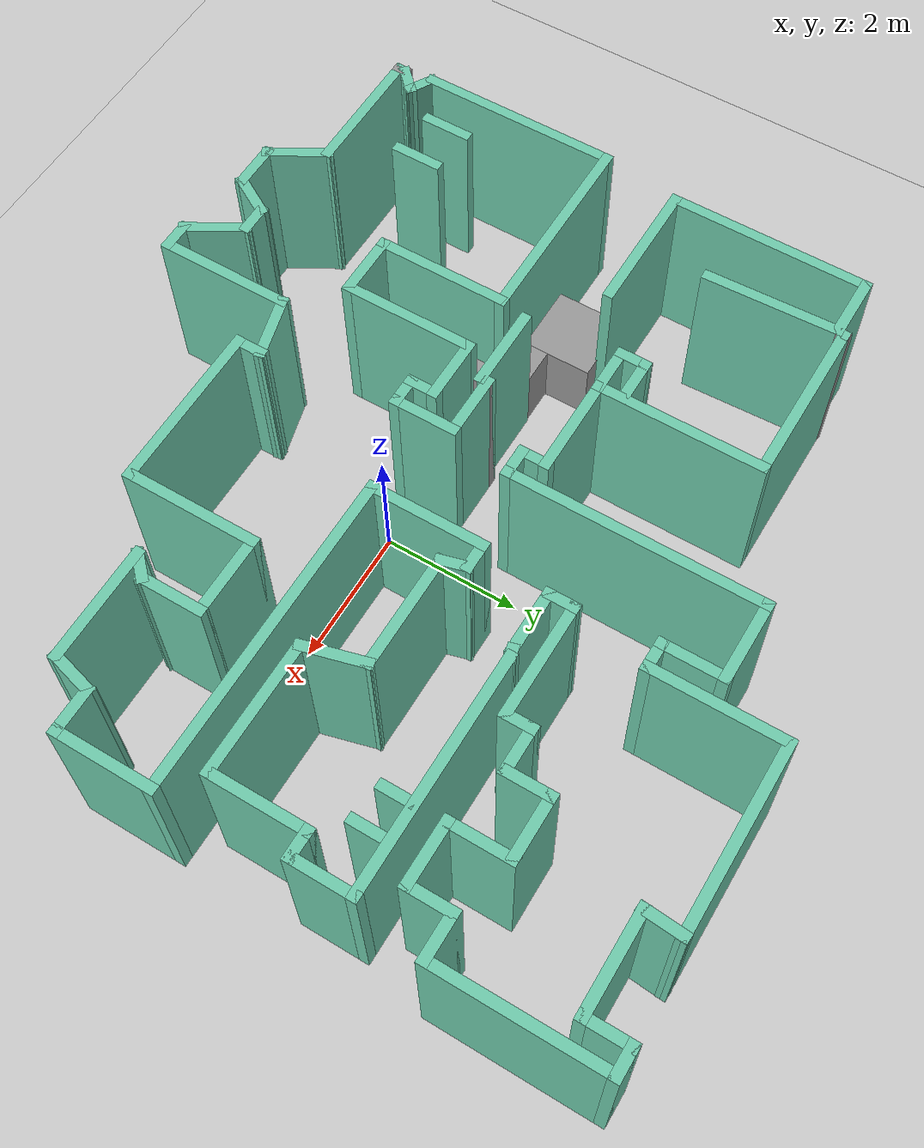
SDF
<sdf version="1.6">
 <world name="default">
  <light name="sun" type="directional">
   <pose>0 0 10 0 -0 0</pose>
   <diffuse>0.8 0.8 0.8 1</diffuse>
   <specular>0.2 0.2 0.2 1</specular>
   <attenuation>
    <range>1000</range>
    <constant>0.9</constant>
    <linear>0.01</linear>
    <quadratic>0.001</quadratic>
   </attenuation>
   <direction>-0.5 0.1 -0.9</direction>
  </light>
  <model name="ground_plane">
   <static>1</static>
   <link name="link">
    <collision name="collision">
     <geometry><plane><normal>0 0 1</normal><size>100 100</size></plane></geometry>
     <surface><friction><ode><mu>100</mu><mu2>50</mu2></ode></friction></surface>
    </collision>
    <visual name="visual">
     <cast_shadows>0</cast_shadows>
     <geometry><plane><normal>0 0 1</normal><size>100 100</size></plane></geometry>
     <material>
      <script><uri>file://media/materials/scripts/gazebo.material</uri><name>Gazebo/Grey</name></script>
     </material>
    </visual>
   </link>
  </model>
  <gravity>0 0 -9.8</gravity>
  <magnetic_field>6e-06 2.3e-05 -4.2e-05</magnetic_field>
  <atmosphere type="adiabatic"/>
  <physics name="default_physics" default="0" type="ode">
   <max_step_size>0.001</max_step_size>
   <real_time_factor>1</real_time_factor>
   <real_time_update_rate>1000</real_time_update_rate>
  </physics>
  <scene><ambient>0.4 0.4 0.4 1</ambient><background>0.7 0.7 0.7 1</background><shadows>1</shadows></scene>
  <spherical_coordinates>
   <surface_model>EARTH_WGS84</surface_model>
   <latitude_deg>0</latitude_deg>
   <longitude_deg>0</longitude_deg>
   <elevation>0</elevation>
   <heading_deg>0</heading_deg>
  </spherical_coordinates>
  <model name="map_28">
   <link name="Wall_0">
    <pose>2.44979 5.13882 0 0 -0 3.14159</pose>
    <visual name="Wall_0_Visual">
     <pose>0 0 1.25 0 -0 0</pose>
     <geometry><box><size>2.75 0.15 2.5</size></box></geometry>
     <material>
      <script><uri>file://media/materials/scripts/gazebo.material</uri><name>Gazebo/Grey</name></script>
      <ambient>0.435294 0.796078 0.67451 1</ambient>
      <shader type="pixel"/>
     </material>
     <meta><layer>0</layer></meta>
    </visual>
    <collision name="Wall_0_Collision">
     <pose>0 0 1.25 0 -0 0</pose>
     <geometry><box><size>2.75 0.15 2.5</size></box></geometry>
     <surface>
      <friction>
       <ode><mu>1</mu><mu2>1</mu2><fdir1>0 0 0</fdir1><slip1>0</slip1><slip2>0</slip2></ode>
       <torsional>
        <coefficient>1</coefficient>
        <patch_radius>0</patch_radius>
        <surface_radius>0</surface_radius>
        <use_patch_radius>1</use_patch_radius>
        <ode><slip>0</slip></ode>
       </torsional>
      </friction>
      <bounce><restitution_coefficient>0</restitution_coefficient><threshold>1e+06</threshold></bounce>
      <contact>
       <collide_without_contact>0</collide_without_contact>
       <collide_without_contact_bitmask>1</collide_without_contact_bitmask>
       <collide_bitmask>1</collide_bitmask>
       <ode>
        <soft_cfm>0</soft_cfm>
        <soft_erp>0.2</soft_erp>
        <kp>1e+13</kp>
        <kd>1</kd>
        <max_vel>0.01</max_vel>
        <min_depth>0</min_depth>
       </ode>
       <bullet>
        <split_impulse>1</split_impulse>
        <split_impulse_penetration_threshold>-0.01</split_impulse_penetration_threshold>
        <soft_cfm>0</soft_cfm>
        <soft_erp>0.2</soft_erp>
        <kp>1e+13</kp>
        <kd>1</kd>
       </bullet>
      </contact>
     </surface>
    </collision>
   </link>
   <link name="Wall_1">
    <pose>1.14979 4.21382 0 0 0 -1.5708</pose>
    <visual name="Wall_1_Visual">
     <pose>0 0 1.25 0 -0 0</pose>
     <geometry><box><size>2 0.15 2.5</size></box></geometry>
     <material>
      <script><uri>file://media/materials/scripts/gazebo.material</uri><name>Gazebo/Grey</name></script>
      <ambient>0.435294 0.796078 0.67451 1</ambient>
      <shader type="pixel"/>
     </material>
     <meta><layer>0</layer></meta>
    </visual>
    <collision name="Wall_1_Collision">
     <pose>0 0 1.25 0 -0 0</pose>
     <geometry><box><size>2 0.15 2.5</size></box></geometry>
     <surface>
      <friction>
       <ode><mu>1</mu><mu2>1</mu2><fdir1>0 0 0</fdir1><slip1>0</slip1><slip2>0</slip2></ode>
       <torsional>
        <coefficient>1</coefficient>
        <patch_radius>0</patch_radius>
        <surface_radius>0</surface_radius>
        <use_patch_radius>1</use_patch_radius>
        <ode><slip>0</slip></ode>
       </torsional>
      </friction>
      <bounce><restitution_coefficient>0</restitution_coefficient><threshold>1e+06</threshold></bounce>
      <contact>
       <collide_without_contact>0</collide_without_contact>
       <collide_without_contact_bitmask>1</collide_without_contact_bitmask>
       <collide_bitmask>1</collide_bitmask>
       <ode>
        <soft_cfm>0</soft_cfm>
        <soft_erp>0.2</soft_erp>
        <kp>1e+13</kp>
        <kd>1</kd>
        <max_vel>0.01</max_vel>
        <min_depth>0</min_depth>
       </ode>
       <bullet>
        <split_impulse>1</split_impulse>
        <split_impulse_penetration_threshold>-0.01</split_impulse_penetration_threshold>
        <soft_cfm>0</soft_cfm>
        <soft_erp>0.2</soft_erp>
        <kp>1e+13</kp>
        <kd>1</kd>
       </bullet>
      </contact>
     </surface>
    </collision>
   </link>
   <link name="Wall_10">
    <pose>-3.17521 3.23882 0 0 -0 3.14159</pose>
    <visual name="Wall_10_Visual">
     <pose>0 0 1.25 0 -0 0</pose>
     <geometry><box><size>2.5 0.15 2.5</size></box></geometry>
     <material>
      <script><uri>file://media/materials/scripts/gazebo.material</uri><name>Gazebo/Grey</name></script>
      <ambient>0.435294 0.796078 0.67451 1</ambient>
      <shader type="pixel"/>
     </material>
     <meta><layer>0</layer></meta>
    </visual>
    <collision name="Wall_10_Collision">
     <pose>0 0 1.25 0 -0 0</pose>
     <geometry><box><size>2.5 0.15 2.5</size></box></geometry>
     <surface>
      <friction>
       <ode><mu>1</mu><mu2>1</mu2><fdir1>0 0 0</fdir1><slip1>0</slip1><slip2>0</slip2></ode>
       <torsional>
        <coefficient>1</coefficient>
        <patch_radius>0</patch_radius>
        <surface_radius>0</surface_radius>
        <use_patch_radius>1</use_patch_radius>
        <ode><slip>0</slip></ode>
       </torsional>
      </friction>
      <bounce><restitution_coefficient>0</restitution_coefficient><threshold>1e+06</threshold></bounce>
      <contact>
       <collide_without_contact>0</collide_without_contact>
       <collide_without_contact_bitmask>1</collide_without_contact_bitmask>
       <collide_bitmask>1</collide_bitmask>
       <ode>
        <soft_cfm>0</soft_cfm>
        <soft_erp>0.2</soft_erp>
        <kp>1e+13</kp>
        <kd>1</kd>
        <max_vel>0.01</max_vel>
        <min_depth>0</min_depth>
       </ode>
       <bullet>
        <split_impulse>1</split_impulse>
        <split_impulse_penetration_threshold>-0.01</split_impulse_penetration_threshold>
        <soft_cfm>0</soft_cfm>
        <soft_erp>0.2</soft_erp>
        <kp>1e+13</kp>
        <kd>1</kd>
       </bullet>
      </contact>
     </surface>
    </collision>
   </link>
   <link name="Wall_100">
    <pose>4.38795 2.27226 0 0 -0 0</pose>
    <visual name="Wall_100_Visual">
     <pose>0 0 1.25 0 -0 0</pose>
     <geometry><box><size>1 0.15 2.5</size></box></geometry>
     <material>
      <script><uri>file://media/materials/scripts/gazebo.material</uri><name>Gazebo/Grey</name></script>
      <ambient>0.435294 0.796078 0.67451 1</ambient>
      <shader type="pixel"/>
     </material>
     <meta><layer>0</layer></meta>
    </visual>
    <collision name="Wall_100_Collision">
     <pose>0 0 1.25 0 -0 0</pose>
     <geometry><box><size>1 0.15 2.5</size></box></geometry>
     <surface>
      <friction>
       <ode><mu>1</mu><mu2>1</mu2><fdir1>0 0 0</fdir1><slip1>0</slip1><slip2>0</slip2></ode>
       <torsional>
        <coefficient>1</coefficient>
        <patch_radius>0</patch_radius>
        <surface_radius>0</surface_radius>
        <use_patch_radius>1</use_patch_radius>
        <ode><slip>0</slip></ode>
       </torsional>
      </friction>
      <bounce><restitution_coefficient>0</restitution_coefficient><threshold>1e+06</threshold></bounce>
      <contact>
       <collide_without_contact>0</collide_without_contact>
       <collide_without_contact_bitmask>1</collide_without_contact_bitmask>
       <collide_bitmask>1</collide_bitmask>
       <ode>
        <soft_cfm>0</soft_cfm>
        <soft_erp>0.2</soft_erp>
        <kp>1e+13</kp>
        <kd>1</kd>
        <max_vel>0.01</max_vel>
        <min_depth>0</min_depth>
       </ode>
       <bullet>
        <split_impulse>1</split_impulse>
        <split_impulse_penetration_threshold>-0.01</split_impulse_penetration_threshold>
        <soft_cfm>0</soft_cfm>
        <soft_erp>0.2</soft_erp>
        <kp>1e+13</kp>
        <kd>1</kd>
       </bullet>
      </contact>
     </surface>
    </collision>
   </link>
   <link name="Wall_101">
    <pose>4.81295 2.57226 0 0 -0 1.5708</pose>
    <visual name="Wall_101_Visual">
     <pose>0 0 1.25 0 -0 0</pose>
     <geometry><box><size>0.75 0.15 2.5</size></box></geometry>
     <material>
      <script><uri>file://media/materials/scripts/gazebo.material</uri><name>Gazebo/Grey</name></script>
      <ambient>0.435294 0.796078 0.67451 1</ambient>
      <shader type="pixel"/>
     </material>
     <meta><layer>0</layer></meta>
    </visual>
    <collision name="Wall_101_Collision">
     <pose>0 0 1.25 0 -0 0</pose>
     <geometry><box><size>0.75 0.15 2.5</size></box></geometry>
     <surface>
      <friction>
       <ode><mu>1</mu><mu2>1</mu2><fdir1>0 0 0</fdir1><slip1>0</slip1><slip2>0</slip2></ode>
       <torsional>
        <coefficient>1</coefficient>
        <patch_radius>0</patch_radius>
        <surface_radius>0</surface_radius>
        <use_patch_radius>1</use_patch_radius>
        <ode><slip>0</slip></ode>
       </torsional>
      </friction>
      <bounce><restitution_coefficient>0</restitution_coefficient><threshold>1e+06</threshold></bounce>
      <contact>
       <collide_without_contact>0</collide_without_contact>
       <collide_without_contact_bitmask>1</collide_without_contact_bitmask>
       <collide_bitmask>1</collide_bitmask>
       <ode>
        <soft_cfm>0</soft_cfm>
        <soft_erp>0.2</soft_erp>
        <kp>1e+13</kp>
        <kd>1</kd>
        <max_vel>0.01</max_vel>
        <min_depth>0</min_depth>
       </ode>
       <bullet>
        <split_impulse>1</split_impulse>
        <split_impulse_penetration_threshold>-0.01</split_impulse_penetration_threshold>
        <soft_cfm>0</soft_cfm>
        <soft_erp>0.2</soft_erp>
        <kp>1e+13</kp>
        <kd>1</kd>
       </bullet>
      </contact>
     </surface>
    </collision>
   </link>
   <link name="Wall_102">
    <pose>5.11295 2.87226 0 0 -0 0</pose>
    <visual name="Wall_102_Visual">
     <pose>0 0 1.25 0 -0 0</pose>
     <geometry><box><size>0.75 0.15 2.5</size></box></geometry>
     <material>
      <script><uri>file://media/materials/scripts/gazebo.material</uri><name>Gazebo/Grey</name></script>
      <ambient>0.435294 0.796078 0.67451 1</ambient>
      <shader type="pixel"/>
     </material>
     <meta><layer>0</layer></meta>
    </visual>
    <collision name="Wall_102_Collision">
     <pose>0 0 1.25 0 -0 0</pose>
     <geometry><box><size>0.75 0.15 2.5</size></box></geometry>
     <surface>
      <friction>
       <ode><mu>1</mu><mu2>1</mu2><fdir1>0 0 0</fdir1><slip1>0</slip1><slip2>0</slip2></ode>
       <torsional>
        <coefficient>1</coefficient>
        <patch_radius>0</patch_radius>
        <surface_radius>0</surface_radius>
        <use_patch_radius>1</use_patch_radius>
        <ode><slip>0</slip></ode>
       </torsional>
      </friction>
      <bounce><restitution_coefficient>0</restitution_coefficient><threshold>1e+06</threshold></bounce>
      <contact>
       <collide_without_contact>0</collide_without_contact>
       <collide_without_contact_bitmask>1</collide_without_contact_bitmask>
       <collide_bitmask>1</collide_bitmask>
       <ode>
        <soft_cfm>0</soft_cfm>
        <soft_erp>0.2</soft_erp>
        <kp>1e+13</kp>
        <kd>1</kd>
        <max_vel>0.01</max_vel>
        <min_depth>0</min_depth>
       </ode>
       <bullet>
        <split_impulse>1</split_impulse>
        <split_impulse_penetration_threshold>-0.01</split_impulse_penetration_threshold>
        <soft_cfm>0</soft_cfm>
        <soft_erp>0.2</soft_erp>
        <kp>1e+13</kp>
        <kd>1</kd>
       </bullet>
      </contact>
     </surface>
    </collision>
   </link>
   <link name="Wall_103">
    <pose>5.41295 4.04726 0 0 -0 1.5708</pose>
    <visual name="Wall_103_Visual">
     <pose>0 0 1.25 0 -0 0</pose>
     <geometry><box><size>2.5 0.15 2.5</size></box></geometry>
     <material>
      <script><uri>file://media/materials/scripts/gazebo.material</uri><name>Gazebo/Grey</name></script>
      <ambient>0.435294 0.796078 0.67451 1</ambient>
      <shader type="pixel"/>
     </material>
     <meta><layer>0</layer></meta>
    </visual>
    <collision name="Wall_103_Collision">
     <pose>0 0 1.25 0 -0 0</pose>
     <geometry><box><size>2.5 0.15 2.5</size></box></geometry>
     <surface>
      <friction>
       <ode><mu>1</mu><mu2>1</mu2><fdir1>0 0 0</fdir1><slip1>0</slip1><slip2>0</slip2></ode>
       <torsional>
        <coefficient>1</coefficient>
        <patch_radius>0</patch_radius>
        <surface_radius>0</surface_radius>
        <use_patch_radius>1</use_patch_radius>
        <ode><slip>0</slip></ode>
       </torsional>
      </friction>
      <bounce><restitution_coefficient>0</restitution_coefficient><threshold>1e+06</threshold></bounce>
      <contact>
       <collide_without_contact>0</collide_without_contact>
       <collide_without_contact_bitmask>1</collide_without_contact_bitmask>
       <collide_bitmask>1</collide_bitmask>
       <ode>
        <soft_cfm>0</soft_cfm>
        <soft_erp>0.2</soft_erp>
        <kp>1e+13</kp>
        <kd>1</kd>
        <max_vel>0.01</max_vel>
        <min_depth>0</min_depth>
       </ode>
       <bullet>
        <split_impulse>1</split_impulse>
        <split_impulse_penetration_threshold>-0.01</split_impulse_penetration_threshold>
        <soft_cfm>0</soft_cfm>
        <soft_erp>0.2</soft_erp>
        <kp>1e+13</kp>
        <kd>1</kd>
       </bullet>
      </contact>
     </surface>
    </collision>
   </link>
   <link name="Wall_104">
    <pose>5.23795 5.22226 0 0 -0 3.14159</pose>
    <visual name="Wall_104_Visual">
     <pose>0 0 1.25 0 -0 0</pose>
     <geometry><box><size>0.5 0.15 2.5</size></box></geometry>
     <material>
      <script><uri>file://media/materials/scripts/gazebo.material</uri><name>Gazebo/Grey</name></script>
      <ambient>0.435294 0.796078 0.67451 1</ambient>
      <shader type="pixel"/>
     </material>
     <meta><layer>0</layer></meta>
    </visual>
    <collision name="Wall_104_Collision">
     <pose>0 0 1.25 0 -0 0</pose>
     <geometry><box><size>0.5 0.15 2.5</size></box></geometry>
     <surface>
      <friction>
       <ode><mu>1</mu><mu2>1</mu2><fdir1>0 0 0</fdir1><slip1>0</slip1><slip2>0</slip2></ode>
       <torsional>
        <coefficient>1</coefficient>
        <patch_radius>0</patch_radius>
        <surface_radius>0</surface_radius>
        <use_patch_radius>1</use_patch_radius>
        <ode><slip>0</slip></ode>
       </torsional>
      </friction>
      <bounce><restitution_coefficient>0</restitution_coefficient><threshold>1e+06</threshold></bounce>
      <contact>
       <collide_without_contact>0</collide_without_contact>
       <collide_without_contact_bitmask>1</collide_without_contact_bitmask>
       <collide_bitmask>1</collide_bitmask>
       <ode>
        <soft_cfm>0</soft_cfm>
        <soft_erp>0.2</soft_erp>
        <kp>1e+13</kp>
        <kd>1</kd>
        <max_vel>0.01</max_vel>
        <min_depth>0</min_depth>
       </ode>
       <bullet>
        <split_impulse>1</split_impulse>
        <split_impulse_penetration_threshold>-0.01</split_impulse_penetration_threshold>
        <soft_cfm>0</soft_cfm>
        <soft_erp>0.2</soft_erp>
        <kp>1e+13</kp>
        <kd>1</kd>
       </bullet>
      </contact>
     </surface>
    </collision>
   </link>
   <link name="Wall_105">
    <pose>5.06295 4.92226 0 0 0 -1.5708</pose>
    <visual name="Wall_105_Visual">
     <pose>0 0 1.25 0 -0 0</pose>
     <geometry><box><size>0.75 0.15 2.5</size></box></geometry>
     <material>
      <script><uri>file://media/materials/scripts/gazebo.material</uri><name>Gazebo/Grey</name></script>
      <ambient>0.435294 0.796078 0.67451 1</ambient>
      <shader type="pixel"/>
     </material>
     <meta><layer>0</layer></meta>
    </visual>
    <collision name="Wall_105_Collision">
     <pose>0 0 1.25 0 -0 0</pose>
     <geometry><box><size>0.75 0.15 2.5</size></box></geometry>
     <surface>
      <friction>
       <ode><mu>1</mu><mu2>1</mu2><fdir1>0 0 0</fdir1><slip1>0</slip1><slip2>0</slip2></ode>
       <torsional>
        <coefficient>1</coefficient>
        <patch_radius>0</patch_radius>
        <surface_radius>0</surface_radius>
        <use_patch_radius>1</use_patch_radius>
        <ode><slip>0</slip></ode>
       </torsional>
      </friction>
      <bounce><restitution_coefficient>0</restitution_coefficient><threshold>1e+06</threshold></bounce>
      <contact>
       <collide_without_contact>0</collide_without_contact>
       <collide_without_contact_bitmask>1</collide_without_contact_bitmask>
       <collide_bitmask>1</collide_bitmask>
       <ode>
        <soft_cfm>0</soft_cfm>
        <soft_erp>0.2</soft_erp>
        <kp>1e+13</kp>
        <kd>1</kd>
        <max_vel>0.01</max_vel>
        <min_depth>0</min_depth>
       </ode>
       <bullet>
        <split_impulse>1</split_impulse>
        <split_impulse_penetration_threshold>-0.01</split_impulse_penetration_threshold>
        <soft_cfm>0</soft_cfm>
        <soft_erp>0.2</soft_erp>
        <kp>1e+13</kp>
        <kd>1</kd>
       </bullet>
      </contact>
     </surface>
    </collision>
   </link>
   <link name="Wall_108">
    <pose>4.38795 4.62226 0 0 -0 3.14159</pose>
    <visual name="Wall_108_Visual">
     <pose>0 0 1.25 0 -0 0</pose>
     <geometry><box><size>1.5 0.15 2.5</size></box></geometry>
     <material>
      <script><uri>file://media/materials/scripts/gazebo.material</uri><name>Gazebo/Grey</name></script>
      <ambient>0.435294 0.796078 0.67451 1</ambient>
      <shader type="pixel"/>
     </material>
     <meta><layer>0</layer></meta>
    </visual>
    <collision name="Wall_108_Collision">
     <pose>0 0 1.25 0 -0 0</pose>
     <geometry><box><size>1.5 0.15 2.5</size></box></geometry>
     <surface>
      <friction>
       <ode><mu>1</mu><mu2>1</mu2><fdir1>0 0 0</fdir1><slip1>0</slip1><slip2>0</slip2></ode>
       <torsional>
        <coefficient>1</coefficient>
        <patch_radius>0</patch_radius>
        <surface_radius>0</surface_radius>
        <use_patch_radius>1</use_patch_radius>
        <ode><slip>0</slip></ode>
       </torsional>
      </friction>
      <bounce><restitution_coefficient>0</restitution_coefficient><threshold>1e+06</threshold></bounce>
      <contact>
       <collide_without_contact>0</collide_without_contact>
       <collide_without_contact_bitmask>1</collide_without_contact_bitmask>
       <collide_bitmask>1</collide_bitmask>
       <ode>
        <soft_cfm>0</soft_cfm>
        <soft_erp>0.2</soft_erp>
        <kp>1e+13</kp>
        <kd>1</kd>
        <max_vel>0.01</max_vel>
        <min_depth>0</min_depth>
       </ode>
       <bullet>
        <split_impulse>1</split_impulse>
        <split_impulse_penetration_threshold>-0.01</split_impulse_penetration_threshold>
        <soft_cfm>0</soft_cfm>
        <soft_erp>0.2</soft_erp>
        <kp>1e+13</kp>
        <kd>1</kd>
       </bullet>
      </contact>
     </surface>
    </collision>
   </link>
   <link name="Wall_109">
    <pose>3.73137 4.88054 0 0 -0 1.4996</pose>
    <visual name="Wall_109_Visual">
     <pose>0 0 1.25 0 -0 0</pose>
     <geometry><box><size>0.667875 0.15 2.5</size></box></geometry>
     <material>
      <script><uri>file://media/materials/scripts/gazebo.material</uri><name>Gazebo/Grey</name></script>
      <ambient>0.435294 0.796078 0.67451 1</ambient>
      <shader type="pixel"/>
     </material>
     <meta><layer>0</layer></meta>
    </visual>
    <collision name="Wall_109_Collision">
     <pose>0 0 1.25 0 -0 0</pose>
     <geometry><box><size>0.667875 0.15 2.5</size></box></geometry>
     <surface>
      <friction>
       <ode><mu>1</mu><mu2>1</mu2><fdir1>0 0 0</fdir1><slip1>0</slip1><slip2>0</slip2></ode>
       <torsional>
        <coefficient>1</coefficient>
        <patch_radius>0</patch_radius>
        <surface_radius>0</surface_radius>
        <use_patch_radius>1</use_patch_radius>
        <ode><slip>0</slip></ode>
       </torsional>
      </friction>
      <bounce><restitution_coefficient>0</restitution_coefficient><threshold>1e+06</threshold></bounce>
      <contact>
       <collide_without_contact>0</collide_without_contact>
       <collide_without_contact_bitmask>1</collide_without_contact_bitmask>
       <collide_bitmask>1</collide_bitmask>
       <ode>
        <soft_cfm>0</soft_cfm>
        <soft_erp>0.2</soft_erp>
        <kp>1e+13</kp>
        <kd>1</kd>
        <max_vel>0.01</max_vel>
        <min_depth>0</min_depth>
       </ode>
       <bullet>
        <split_impulse>1</split_impulse>
        <split_impulse_penetration_threshold>-0.01</split_impulse_penetration_threshold>
        <soft_cfm>0</soft_cfm>
        <soft_erp>0.2</soft_erp>
        <kp>1e+13</kp>
        <kd>1</kd>
       </bullet>
      </contact>
     </surface>
    </collision>
   </link>
   <link name="Wall_11">
    <pose>-4.3502 3.23882 0 0 -0 0</pose>
    <visual name="Wall_11_Visual">
     <pose>0 0 1.25 0 -0 0</pose>
     <geometry><box><size>0.15 0.15 2.5</size></box></geometry>
     <material>
      <script><uri>file://media/materials/scripts/gazebo.material</uri><name>Gazebo/Grey</name></script>
      <ambient>0.435294 0.796078 0.67451 1</ambient>
      <shader type="pixel"/>
     </material>
     <meta><layer>0</layer></meta>
    </visual>
    <collision name="Wall_11_Collision">
     <pose>0 0 1.25 0 -0 0</pose>
     <geometry><box><size>0.15 0.15 2.5</size></box></geometry>
     <surface>
      <friction>
       <ode><mu>1</mu><mu2>1</mu2><fdir1>0 0 0</fdir1><slip1>0</slip1><slip2>0</slip2></ode>
       <torsional>
        <coefficient>1</coefficient>
        <patch_radius>0</patch_radius>
        <surface_radius>0</surface_radius>
        <use_patch_radius>1</use_patch_radius>
        <ode><slip>0</slip></ode>
       </torsional>
      </friction>
      <bounce><restitution_coefficient>0</restitution_coefficient><threshold>1e+06</threshold></bounce>
      <contact>
       <collide_without_contact>0</collide_without_contact>
       <collide_without_contact_bitmask>1</collide_without_contact_bitmask>
       <collide_bitmask>1</collide_bitmask>
       <ode>
        <soft_cfm>0</soft_cfm>
        <soft_erp>0.2</soft_erp>
        <kp>1e+13</kp>
        <kd>1</kd>
        <max_vel>0.01</max_vel>
        <min_depth>0</min_depth>
       </ode>
       <bullet>
        <split_impulse>1</split_impulse>
        <split_impulse_penetration_threshold>-0.01</split_impulse_penetration_threshold>
        <soft_cfm>0</soft_cfm>
        <soft_erp>0.2</soft_erp>
        <kp>1e+13</kp>
        <kd>1</kd>
       </bullet>
      </contact>
     </surface>
    </collision>
   </link>
   <link name="Wall_114">
    <pose>-4.33787 2.20912 0 0 -0 1.61173</pose>
    <visual name="Wall_114_Visual">
     <pose>0 0 1.25 0 -0 0</pose>
     <geometry><box><size>2.01778 0.15 2.5</size></box></geometry>
     <material>
      <script><uri>file://media/materials/scripts/gazebo.material</uri><name>Gazebo/Grey</name></script>
      <ambient>0.435294 0.796078 0.67451 1</ambient>
      <shader type="pixel"/>
     </material>
     <meta><layer>0</layer></meta>
    </visual>
    <collision name="Wall_114_Collision">
     <pose>0 0 1.25 0 -0 0</pose>
     <geometry><box><size>2.01778 0.15 2.5</size></box></geometry>
     <surface>
      <friction>
       <ode><mu>1</mu><mu2>1</mu2><fdir1>0 0 0</fdir1><slip1>0</slip1><slip2>0</slip2></ode>
       <torsional>
        <coefficient>1</coefficient>
        <patch_radius>0</patch_radius>
        <surface_radius>0</surface_radius>
        <use_patch_radius>1</use_patch_radius>
        <ode><slip>0</slip></ode>
       </torsional>
      </friction>
      <bounce><restitution_coefficient>0</restitution_coefficient><threshold>1e+06</threshold></bounce>
      <contact>
       <collide_without_contact>0</collide_without_contact>
       <collide_without_contact_bitmask>1</collide_without_contact_bitmask>
       <collide_bitmask>1</collide_bitmask>
       <ode>
        <soft_cfm>0</soft_cfm>
        <soft_erp>0.2</soft_erp>
        <kp>1e+13</kp>
        <kd>1</kd>
        <max_vel>0.01</max_vel>
        <min_depth>0</min_depth>
       </ode>
       <bullet>
        <split_impulse>1</split_impulse>
        <split_impulse_penetration_threshold>-0.01</split_impulse_penetration_threshold>
        <soft_cfm>0</soft_cfm>
        <soft_erp>0.2</soft_erp>
        <kp>1e+13</kp>
        <kd>1</kd>
       </bullet>
      </contact>
     </surface>
    </collision>
   </link>
   <link name="Wall_118">
    <pose>-2.30021 0.888824 0 0 -0 3.14159</pose>
    <visual name="Wall_118_Visual">
     <pose>0 0 1.25 0 -0 0</pose>
     <geometry><box><size>0.75 0.15 2.5</size></box></geometry>
     <material>
      <script><uri>file://media/materials/scripts/gazebo.material</uri><name>Gazebo/Grey</name></script>
      <ambient>0.435294 0.796078 0.67451 1</ambient>
      <shader type="pixel"/>
     </material>
     <meta><layer>0</layer></meta>
    </visual>
    <collision name="Wall_118_Collision">
     <pose>0 0 1.25 0 -0 0</pose>
     <geometry><box><size>0.75 0.15 2.5</size></box></geometry>
     <surface>
      <friction>
       <ode><mu>1</mu><mu2>1</mu2><fdir1>0 0 0</fdir1><slip1>0</slip1><slip2>0</slip2></ode>
       <torsional>
        <coefficient>1</coefficient>
        <patch_radius>0</patch_radius>
        <surface_radius>0</surface_radius>
        <use_patch_radius>1</use_patch_radius>
        <ode><slip>0</slip></ode>
       </torsional>
      </friction>
      <bounce><restitution_coefficient>0</restitution_coefficient><threshold>1e+06</threshold></bounce>
      <contact>
       <collide_without_contact>0</collide_without_contact>
       <collide_without_contact_bitmask>1</collide_without_contact_bitmask>
       <collide_bitmask>1</collide_bitmask>
       <ode>
        <soft_cfm>0</soft_cfm>
        <soft_erp>0.2</soft_erp>
        <kp>1e+13</kp>
        <kd>1</kd>
        <max_vel>0.01</max_vel>
        <min_depth>0</min_depth>
       </ode>
       <bullet>
        <split_impulse>1</split_impulse>
        <split_impulse_penetration_threshold>-0.01</split_impulse_penetration_threshold>
        <soft_cfm>0</soft_cfm>
        <soft_erp>0.2</soft_erp>
        <kp>1e+13</kp>
        <kd>1</kd>
       </bullet>
      </contact>
     </surface>
    </collision>
   </link>
   <link name="Wall_119">
    <pose>-2.6002 1.06382 0 0 -0 1.5708</pose>
    <visual name="Wall_119_Visual">
     <pose>0 0 1.25 0 -0 0</pose>
     <geometry><box><size>0.5 0.15 2.5</size></box></geometry>
     <material>
      <script><uri>file://media/materials/scripts/gazebo.material</uri><name>Gazebo/Grey</name></script>
      <ambient>0.435294 0.796078 0.67451 1</ambient>
      <shader type="pixel"/>
     </material>
     <meta><layer>0</layer></meta>
    </visual>
    <collision name="Wall_119_Collision">
     <pose>0 0 1.25 0 -0 0</pose>
     <geometry><box><size>0.5 0.15 2.5</size></box></geometry>
     <surface>
      <friction>
       <ode><mu>1</mu><mu2>1</mu2><fdir1>0 0 0</fdir1><slip1>0</slip1><slip2>0</slip2></ode>
       <torsional>
        <coefficient>1</coefficient>
        <patch_radius>0</patch_radius>
        <surface_radius>0</surface_radius>
        <use_patch_radius>1</use_patch_radius>
        <ode><slip>0</slip></ode>
       </torsional>
      </friction>
      <bounce><restitution_coefficient>0</restitution_coefficient><threshold>1e+06</threshold></bounce>
      <contact>
       <collide_without_contact>0</collide_without_contact>
       <collide_without_contact_bitmask>1</collide_without_contact_bitmask>
       <collide_bitmask>1</collide_bitmask>
       <ode>
        <soft_cfm>0</soft_cfm>
        <soft_erp>0.2</soft_erp>
        <kp>1e+13</kp>
        <kd>1</kd>
        <max_vel>0.01</max_vel>
        <min_depth>0</min_depth>
       </ode>
       <bullet>
        <split_impulse>1</split_impulse>
        <split_impulse_penetration_threshold>-0.01</split_impulse_penetration_threshold>
        <soft_cfm>0</soft_cfm>
        <soft_erp>0.2</soft_erp>
        <kp>1e+13</kp>
        <kd>1</kd>
       </bullet>
      </contact>
     </surface>
    </collision>
   </link>
   <link name="Wall_120">
    <pose>-2.30021 1.23882 0 0 -0 0</pose>
    <visual name="Wall_120_Visual">
     <pose>0 0 1.25 0 -0 0</pose>
     <geometry><box><size>0.75 0.15 2.5</size></box></geometry>
     <material>
      <script><uri>file://media/materials/scripts/gazebo.material</uri><name>Gazebo/Grey</name></script>
      <ambient>0.435294 0.796078 0.67451 1</ambient>
      <shader type="pixel"/>
     </material>
     <meta><layer>0</layer></meta>
    </visual>
    <collision name="Wall_120_Collision">
     <pose>0 0 1.25 0 -0 0</pose>
     <geometry><box><size>0.75 0.15 2.5</size></box></geometry>
     <surface>
      <friction>
       <ode><mu>1</mu><mu2>1</mu2><fdir1>0 0 0</fdir1><slip1>0</slip1><slip2>0</slip2></ode>
       <torsional>
        <coefficient>1</coefficient>
        <patch_radius>0</patch_radius>
        <surface_radius>0</surface_radius>
        <use_patch_radius>1</use_patch_radius>
        <ode><slip>0</slip></ode>
       </torsional>
      </friction>
      <bounce><restitution_coefficient>0</restitution_coefficient><threshold>1e+06</threshold></bounce>
      <contact>
       <collide_without_contact>0</collide_without_contact>
       <collide_without_contact_bitmask>1</collide_without_contact_bitmask>
       <collide_bitmask>1</collide_bitmask>
       <ode>
        <soft_cfm>0</soft_cfm>
        <soft_erp>0.2</soft_erp>
        <kp>1e+13</kp>
        <kd>1</kd>
        <max_vel>0.01</max_vel>
        <min_depth>0</min_depth>
       </ode>
       <bullet>
        <split_impulse>1</split_impulse>
        <split_impulse_penetration_threshold>-0.01</split_impulse_penetration_threshold>
        <soft_cfm>0</soft_cfm>
        <soft_erp>0.2</soft_erp>
        <kp>1e+13</kp>
        <kd>1</kd>
       </bullet>
      </contact>
     </surface>
    </collision>
   </link>
   <link name="Wall_124">
    <pose>3.9811 1.60989 0 0 0 -1.5708</pose>
    <visual name="Wall_124_Visual">
     <pose>0 0 1.25 0 -0 0</pose>
     <geometry><box><size>0.5 0.15 2.5</size></box></geometry>
     <material>
      <script><uri>file://media/materials/scripts/gazebo.material</uri><name>Gazebo/Grey</name></script>
      <ambient>0.435294 0.796078 0.67451 1</ambient>
      <shader type="pixel"/>
     </material>
     <meta><layer>0</layer></meta>
    </visual>
    <collision name="Wall_124_Collision">
     <pose>0 0 1.25 0 -0 0</pose>
     <geometry><box><size>0.5 0.15 2.5</size></box></geometry>
     <surface>
      <friction>
       <ode><mu>1</mu><mu2>1</mu2><fdir1>0 0 0</fdir1><slip1>0</slip1><slip2>0</slip2></ode>
       <torsional>
        <coefficient>1</coefficient>
        <patch_radius>0</patch_radius>
        <surface_radius>0</surface_radius>
        <use_patch_radius>1</use_patch_radius>
        <ode><slip>0</slip></ode>
       </torsional>
      </friction>
      <bounce><restitution_coefficient>0</restitution_coefficient><threshold>1e+06</threshold></bounce>
      <contact>
       <collide_without_contact>0</collide_without_contact>
       <collide_without_contact_bitmask>1</collide_without_contact_bitmask>
       <collide_bitmask>1</collide_bitmask>
       <ode>
        <soft_cfm>0</soft_cfm>
        <soft_erp>0.2</soft_erp>
        <kp>1e+13</kp>
        <kd>1</kd>
        <max_vel>0.01</max_vel>
        <min_depth>0</min_depth>
       </ode>
       <bullet>
        <split_impulse>1</split_impulse>
        <split_impulse_penetration_threshold>-0.01</split_impulse_penetration_threshold>
        <soft_cfm>0</soft_cfm>
        <soft_erp>0.2</soft_erp>
        <kp>1e+13</kp>
        <kd>1</kd>
       </bullet>
      </contact>
     </surface>
    </collision>
   </link>
   <link name="Wall_126">
    <pose>4.48997 1.54049 0 0 0 -1.5708</pose>
    <visual name="Wall_126_Visual">
     <pose>0 0 1.25 0 -0 0</pose>
     <geometry><box><size>0.5 0.15 2.5</size></box></geometry>
     <material>
      <script><uri>file://media/materials/scripts/gazebo.material</uri><name>Gazebo/Grey</name></script>
      <ambient>0.435294 0.796078 0.67451 1</ambient>
      <shader type="pixel"/>
     </material>
     <meta><layer>0</layer></meta>
    </visual>
    <collision name="Wall_126_Collision">
     <pose>0 0 1.25 0 -0 0</pose>
     <geometry><box><size>0.5 0.15 2.5</size></box></geometry>
     <surface>
      <friction>
       <ode><mu>1</mu><mu2>1</mu2><fdir1>0 0 0</fdir1><slip1>0</slip1><slip2>0</slip2></ode>
       <torsional>
        <coefficient>1</coefficient>
        <patch_radius>0</patch_radius>
        <surface_radius>0</surface_radius>
        <use_patch_radius>1</use_patch_radius>
        <ode><slip>0</slip></ode>
       </torsional>
      </friction>
      <bounce><restitution_coefficient>0</restitution_coefficient><threshold>1e+06</threshold></bounce>
      <contact>
       <collide_without_contact>0</collide_without_contact>
       <collide_without_contact_bitmask>1</collide_without_contact_bitmask>
       <collide_bitmask>1</collide_bitmask>
       <ode>
        <soft_cfm>0</soft_cfm>
        <soft_erp>0.2</soft_erp>
        <kp>1e+13</kp>
        <kd>1</kd>
        <max_vel>0.01</max_vel>
        <min_depth>0</min_depth>
       </ode>
       <bullet>
        <split_impulse>1</split_impulse>
        <split_impulse_penetration_threshold>-0.01</split_impulse_penetration_threshold>
        <soft_cfm>0</soft_cfm>
        <soft_erp>0.2</soft_erp>
        <kp>1e+13</kp>
        <kd>1</kd>
       </bullet>
      </contact>
     </surface>
    </collision>
   </link>
   <link name="Wall_130">
    <pose>-4.73914 -3.07184 0 0 0 -1.5708</pose>
    <visual name="Wall_130_Visual">
     <pose>0 0 1.25 0 -0 0</pose>
     <geometry><box><size>0.75 0.15 2.5</size></box></geometry>
     <material>
      <script><uri>file://media/materials/scripts/gazebo.material</uri><name>Gazebo/Grey</name></script>
      <ambient>0.435294 0.796078 0.67451 1</ambient>
      <shader type="pixel"/>
     </material>
     <meta><layer>0</layer></meta>
    </visual>
    <collision name="Wall_130_Collision">
     <pose>0 0 1.25 0 -0 0</pose>
     <geometry><box><size>0.75 0.15 2.5</size></box></geometry>
     <surface>
      <friction>
       <ode><mu>1</mu><mu2>1</mu2><fdir1>0 0 0</fdir1><slip1>0</slip1><slip2>0</slip2></ode>
       <torsional>
        <coefficient>1</coefficient>
        <patch_radius>0</patch_radius>
        <surface_radius>0</surface_radius>
        <use_patch_radius>1</use_patch_radius>
        <ode><slip>0</slip></ode>
       </torsional>
      </friction>
      <bounce><restitution_coefficient>0</restitution_coefficient><threshold>1e+06</threshold></bounce>
      <contact>
       <collide_without_contact>0</collide_without_contact>
       <collide_without_contact_bitmask>1</collide_without_contact_bitmask>
       <collide_bitmask>1</collide_bitmask>
       <ode>
        <soft_cfm>0</soft_cfm>
        <soft_erp>0.2</soft_erp>
        <kp>1e+13</kp>
        <kd>1</kd>
        <max_vel>0.01</max_vel>
        <min_depth>0</min_depth>
       </ode>
       <bullet>
        <split_impulse>1</split_impulse>
        <split_impulse_penetration_threshold>-0.01</split_impulse_penetration_threshold>
        <soft_cfm>0</soft_cfm>
        <soft_erp>0.2</soft_erp>
        <kp>1e+13</kp>
        <kd>1</kd>
       </bullet>
      </contact>
     </surface>
    </collision>
   </link>
   <link name="Wall_132">
    <pose>-4.06835 -3.14124 0 0 0 -1.5708</pose>
    <visual name="Wall_132_Visual">
     <pose>0 0 1.25 0 -0 0</pose>
     <geometry><box><size>0.75 0.15 2.5</size></box></geometry>
     <material>
      <script><uri>file://media/materials/scripts/gazebo.material</uri><name>Gazebo/Grey</name></script>
      <ambient>0.435294 0.796078 0.67451 1</ambient>
      <shader type="pixel"/>
     </material>
     <meta><layer>0</layer></meta>
    </visual>
    <collision name="Wall_132_Collision">
     <pose>0 0 1.25 0 -0 0</pose>
     <geometry><box><size>0.75 0.15 2.5</size></box></geometry>
     <surface>
      <friction>
       <ode><mu>1</mu><mu2>1</mu2><fdir1>0 0 0</fdir1><slip1>0</slip1><slip2>0</slip2></ode>
       <torsional>
        <coefficient>1</coefficient>
        <patch_radius>0</patch_radius>
        <surface_radius>0</surface_radius>
        <use_patch_radius>1</use_patch_radius>
        <ode><slip>0</slip></ode>
       </torsional>
      </friction>
      <bounce><restitution_coefficient>0</restitution_coefficient><threshold>1e+06</threshold></bounce>
      <contact>
       <collide_without_contact>0</collide_without_contact>
       <collide_without_contact_bitmask>1</collide_without_contact_bitmask>
       <collide_bitmask>1</collide_bitmask>
       <ode>
        <soft_cfm>0</soft_cfm>
        <soft_erp>0.2</soft_erp>
        <kp>1e+13</kp>
        <kd>1</kd>
        <max_vel>0.01</max_vel>
        <min_depth>0</min_depth>
       </ode>
       <bullet>
        <split_impulse>1</split_impulse>
        <split_impulse_penetration_threshold>-0.01</split_impulse_penetration_threshold>
        <soft_cfm>0</soft_cfm>
        <soft_erp>0.2</soft_erp>
        <kp>1e+13</kp>
        <kd>1</kd>
       </bullet>
      </contact>
     </surface>
    </collision>
   </link>
   <link name="Wall_14">
    <pose>-4.36315 3.19053 0 0 0 -1.8326</pose>
    <visual name="Wall_14_Visual">
     <pose>0 0 1.25 0 -0 0</pose>
     <geometry><box><size>0.25 0.15 2.5</size></box></geometry>
     <material>
      <script><uri>file://media/materials/scripts/gazebo.material</uri><name>Gazebo/Grey</name></script>
      <ambient>1 1 1 1</ambient>
      <shader type="pixel"/>
     </material>
     <meta><layer>0</layer></meta>
    </visual>
    <collision name="Wall_14_Collision">
     <pose>0 0 1.25 0 -0 0</pose>
     <geometry><box><size>0.25 0.15 2.5</size></box></geometry>
     <surface>
      <friction>
       <ode><mu>1</mu><mu2>1</mu2><fdir1>0 0 0</fdir1><slip1>0</slip1><slip2>0</slip2></ode>
       <torsional>
        <coefficient>1</coefficient>
        <patch_radius>0</patch_radius>
        <surface_radius>0</surface_radius>
        <use_patch_radius>1</use_patch_radius>
        <ode><slip>0</slip></ode>
       </torsional>
      </friction>
      <bounce><restitution_coefficient>0</restitution_coefficient><threshold>1e+06</threshold></bounce>
      <contact>
       <collide_without_contact>0</collide_without_contact>
       <collide_without_contact_bitmask>1</collide_without_contact_bitmask>
       <collide_bitmask>1</collide_bitmask>
       <ode>
        <soft_cfm>0</soft_cfm>
        <soft_erp>0.2</soft_erp>
        <kp>1e+13</kp>
        <kd>1</kd>
        <max_vel>0.01</max_vel>
        <min_depth>0</min_depth>
       </ode>
       <bullet>
        <split_impulse>1</split_impulse>
        <split_impulse_penetration_threshold>-0.01</split_impulse_penetration_threshold>
        <soft_cfm>0</soft_cfm>
        <soft_erp>0.2</soft_erp>
        <kp>1e+13</kp>
        <kd>1</kd>
       </bullet>
      </contact>
     </surface>
    </collision>
   </link>
   <link name="Wall_15">
    <pose>-4.80109 3.14223 0 0 -0 3.14159</pose>
    <visual name="Wall_15_Visual">
     <pose>0 0 1.25 0 -0 0</pose>
     <geometry><box><size>1 0.15 2.5</size></box></geometry>
     <material>
      <script><uri>file://media/materials/scripts/gazebo.material</uri><name>Gazebo/Grey</name></script>
      <ambient>0.435294 0.796078 0.67451 1</ambient>
      <shader type="pixel"/>
     </material>
     <meta><layer>0</layer></meta>
    </visual>
    <collision name="Wall_15_Collision">
     <pose>0 0 1.25 0 -0 0</pose>
     <geometry><box><size>1 0.15 2.5</size></box></geometry>
     <surface>
      <friction>
       <ode><mu>1</mu><mu2>1</mu2><fdir1>0 0 0</fdir1><slip1>0</slip1><slip2>0</slip2></ode>
       <torsional>
        <coefficient>1</coefficient>
        <patch_radius>0</patch_radius>
        <surface_radius>0</surface_radius>
        <use_patch_radius>1</use_patch_radius>
        <ode><slip>0</slip></ode>
       </torsional>
      </friction>
      <bounce><restitution_coefficient>0</restitution_coefficient><threshold>1e+06</threshold></bounce>
      <contact>
       <collide_without_contact>0</collide_without_contact>
       <collide_without_contact_bitmask>1</collide_without_contact_bitmask>
       <collide_bitmask>1</collide_bitmask>
       <ode>
        <soft_cfm>0</soft_cfm>
        <soft_erp>0.2</soft_erp>
        <kp>1e+13</kp>
        <kd>1</kd>
        <max_vel>0.01</max_vel>
        <min_depth>0</min_depth>
       </ode>
       <bullet>
        <split_impulse>1</split_impulse>
        <split_impulse_penetration_threshold>-0.01</split_impulse_penetration_threshold>
        <soft_cfm>0</soft_cfm>
        <soft_erp>0.2</soft_erp>
        <kp>1e+13</kp>
        <kd>1</kd>
       </bullet>
      </contact>
     </surface>
    </collision>
   </link>
   <link name="Wall_16">
    <pose>-5.22609 1.71723 0 0 0 -1.5708</pose>
    <visual name="Wall_16_Visual">
     <pose>0 0 1.25 0 -0 0</pose>
     <geometry><box><size>3 0.15 2.5</size></box></geometry>
     <material>
      <script><uri>file://media/materials/scripts/gazebo.material</uri><name>Gazebo/Grey</name></script>
      <ambient>0.435294 0.796078 0.67451 1</ambient>
      <shader type="pixel"/>
     </material>
     <meta><layer>0</layer></meta>
    </visual>
    <collision name="Wall_16_Collision">
     <pose>0 0 1.25 0 -0 0</pose>
     <geometry><box><size>3 0.15 2.5</size></box></geometry>
     <surface>
      <friction>
       <ode><mu>1</mu><mu2>1</mu2><fdir1>0 0 0</fdir1><slip1>0</slip1><slip2>0</slip2></ode>
       <torsional>
        <coefficient>1</coefficient>
        <patch_radius>0</patch_radius>
        <surface_radius>0</surface_radius>
        <use_patch_radius>1</use_patch_radius>
        <ode><slip>0</slip></ode>
       </torsional>
      </friction>
      <bounce><restitution_coefficient>0</restitution_coefficient><threshold>1e+06</threshold></bounce>
      <contact>
       <collide_without_contact>0</collide_without_contact>
       <collide_without_contact_bitmask>1</collide_without_contact_bitmask>
       <collide_bitmask>1</collide_bitmask>
       <ode>
        <soft_cfm>0</soft_cfm>
        <soft_erp>0.2</soft_erp>
        <kp>1e+13</kp>
        <kd>1</kd>
        <max_vel>0.01</max_vel>
        <min_depth>0</min_depth>
       </ode>
       <bullet>
        <split_impulse>1</split_impulse>
        <split_impulse_penetration_threshold>-0.01</split_impulse_penetration_threshold>
        <soft_cfm>0</soft_cfm>
        <soft_erp>0.2</soft_erp>
        <kp>1e+13</kp>
        <kd>1</kd>
       </bullet>
      </contact>
     </surface>
    </collision>
   </link>
   <link name="Wall_17">
    <pose>-4.30109 0.292231 0 0 -0 0</pose>
    <visual name="Wall_17_Visual">
     <pose>0 0 1.25 0 -0 0</pose>
     <geometry><box><size>2 0.15 2.5</size></box></geometry>
     <material>
      <script><uri>file://media/materials/scripts/gazebo.material</uri><name>Gazebo/Grey</name></script>
      <ambient>0.435294 0.796078 0.67451 1</ambient>
      <shader type="pixel"/>
     </material>
     <meta><layer>0</layer></meta>
    </visual>
    <collision name="Wall_17_Collision">
     <pose>0 0 1.25 0 -0 0</pose>
     <geometry><box><size>2 0.15 2.5</size></box></geometry>
     <surface>
      <friction>
       <ode><mu>1</mu><mu2>1</mu2><fdir1>0 0 0</fdir1><slip1>0</slip1><slip2>0</slip2></ode>
       <torsional>
        <coefficient>1</coefficient>
        <patch_radius>0</patch_radius>
        <surface_radius>0</surface_radius>
        <use_patch_radius>1</use_patch_radius>
        <ode><slip>0</slip></ode>
       </torsional>
      </friction>
      <bounce><restitution_coefficient>0</restitution_coefficient><threshold>1e+06</threshold></bounce>
      <contact>
       <collide_without_contact>0</collide_without_contact>
       <collide_without_contact_bitmask>1</collide_without_contact_bitmask>
       <collide_bitmask>1</collide_bitmask>
       <ode>
        <soft_cfm>0</soft_cfm>
        <soft_erp>0.2</soft_erp>
        <kp>1e+13</kp>
        <kd>1</kd>
        <max_vel>0.01</max_vel>
        <min_depth>0</min_depth>
       </ode>
       <bullet>
        <split_impulse>1</split_impulse>
        <split_impulse_penetration_threshold>-0.01</split_impulse_penetration_threshold>
        <soft_cfm>0</soft_cfm>
        <soft_erp>0.2</soft_erp>
        <kp>1e+13</kp>
        <kd>1</kd>
       </bullet>
      </contact>
     </surface>
    </collision>
   </link>
   <link name="Wall_2">
    <pose>0.974795 3.28882 0 0 -0 3.14159</pose>
    <visual name="Wall_2_Visual">
     <pose>0 0 1.25 0 -0 0</pose>
     <geometry><box><size>0.5 0.15 2.5</size></box></geometry>
     <material>
      <script><uri>file://media/materials/scripts/gazebo.material</uri><name>Gazebo/Grey</name></script>
      <ambient>0.435294 0.796078 0.67451 1</ambient>
      <shader type="pixel"/>
     </material>
     <meta><layer>0</layer></meta>
    </visual>
    <collision name="Wall_2_Collision">
     <pose>0 0 1.25 0 -0 0</pose>
     <geometry><box><size>0.5 0.15 2.5</size></box></geometry>
     <surface>
      <friction>
       <ode><mu>1</mu><mu2>1</mu2><fdir1>0 0 0</fdir1><slip1>0</slip1><slip2>0</slip2></ode>
       <torsional>
        <coefficient>1</coefficient>
        <patch_radius>0</patch_radius>
        <surface_radius>0</surface_radius>
        <use_patch_radius>1</use_patch_radius>
        <ode><slip>0</slip></ode>
       </torsional>
      </friction>
      <bounce><restitution_coefficient>0</restitution_coefficient><threshold>1e+06</threshold></bounce>
      <contact>
       <collide_without_contact>0</collide_without_contact>
       <collide_without_contact_bitmask>1</collide_without_contact_bitmask>
       <collide_bitmask>1</collide_bitmask>
       <ode>
        <soft_cfm>0</soft_cfm>
        <soft_erp>0.2</soft_erp>
        <kp>1e+13</kp>
        <kd>1</kd>
        <max_vel>0.01</max_vel>
        <min_depth>0</min_depth>
       </ode>
       <bullet>
        <split_impulse>1</split_impulse>
        <split_impulse_penetration_threshold>-0.01</split_impulse_penetration_threshold>
        <soft_cfm>0</soft_cfm>
        <soft_erp>0.2</soft_erp>
        <kp>1e+13</kp>
        <kd>1</kd>
       </bullet>
      </contact>
     </surface>
    </collision>
   </link>
   <link name="Wall_23">
    <pose>-1.8855 -0.469695 0 0 -0 0</pose>
    <visual name="Wall_23_Visual">
     <pose>0 0 1.25 0 -0 0</pose>
     <geometry><box><size>1.25 0.15 2.5</size></box></geometry>
     <material>
      <script><uri>file://media/materials/scripts/gazebo.material</uri><name>Gazebo/Grey</name></script>
      <ambient>0.435294 0.796078 0.67451 1</ambient>
      <shader type="pixel"/>
     </material>
     <meta><layer>0</layer></meta>
    </visual>
    <collision name="Wall_23_Collision">
     <pose>0 0 1.25 0 -0 0</pose>
     <geometry><box><size>1.25 0.15 2.5</size></box></geometry>
     <surface>
      <friction>
       <ode><mu>1</mu><mu2>1</mu2><fdir1>0 0 0</fdir1><slip1>0</slip1><slip2>0</slip2></ode>
       <torsional>
        <coefficient>1</coefficient>
        <patch_radius>0</patch_radius>
        <surface_radius>0</surface_radius>
        <use_patch_radius>1</use_patch_radius>
        <ode><slip>0</slip></ode>
       </torsional>
      </friction>
      <bounce><restitution_coefficient>0</restitution_coefficient><threshold>1e+06</threshold></bounce>
      <contact>
       <collide_without_contact>0</collide_without_contact>
       <collide_without_contact_bitmask>1</collide_without_contact_bitmask>
       <collide_bitmask>1</collide_bitmask>
       <ode>
        <soft_cfm>0</soft_cfm>
        <soft_erp>0.2</soft_erp>
        <kp>1e+13</kp>
        <kd>1</kd>
        <max_vel>0.01</max_vel>
        <min_depth>0</min_depth>
       </ode>
       <bullet>
        <split_impulse>1</split_impulse>
        <split_impulse_penetration_threshold>-0.01</split_impulse_penetration_threshold>
        <soft_cfm>0</soft_cfm>
        <soft_erp>0.2</soft_erp>
        <kp>1e+13</kp>
        <kd>1</kd>
       </bullet>
      </contact>
     </surface>
    </collision>
   </link>
   <link name="Wall_24">
    <pose>-1.3355 -0.419695 0 0 -0 1.5708</pose>
    <visual name="Wall_24_Visual">
     <pose>0 0 1.25 0 -0 0</pose>
     <geometry><box><size>0.25 0.15 2.5</size></box></geometry>
     <material>
      <script><uri>file://media/materials/scripts/gazebo.material</uri><name>Gazebo/Grey</name></script>
      <ambient>1 1 1 1</ambient>
      <shader type="pixel"/>
     </material>
     <meta><layer>0</layer></meta>
    </visual>
    <collision name="Wall_24_Collision">
     <pose>0 0 1.25 0 -0 0</pose>
     <geometry><box><size>0.25 0.15 2.5</size></box></geometry>
     <surface>
      <friction>
       <ode><mu>1</mu><mu2>1</mu2><fdir1>0 0 0</fdir1><slip1>0</slip1><slip2>0</slip2></ode>
       <torsional>
        <coefficient>1</coefficient>
        <patch_radius>0</patch_radius>
        <surface_radius>0</surface_radius>
        <use_patch_radius>1</use_patch_radius>
        <ode><slip>0</slip></ode>
       </torsional>
      </friction>
      <bounce><restitution_coefficient>0</restitution_coefficient><threshold>1e+06</threshold></bounce>
      <contact>
       <collide_without_contact>0</collide_without_contact>
       <collide_without_contact_bitmask>1</collide_without_contact_bitmask>
       <collide_bitmask>1</collide_bitmask>
       <ode>
        <soft_cfm>0</soft_cfm>
        <soft_erp>0.2</soft_erp>
        <kp>1e+13</kp>
        <kd>1</kd>
        <max_vel>0.01</max_vel>
        <min_depth>0</min_depth>
       </ode>
       <bullet>
        <split_impulse>1</split_impulse>
        <split_impulse_penetration_threshold>-0.01</split_impulse_penetration_threshold>
        <soft_cfm>0</soft_cfm>
        <soft_erp>0.2</soft_erp>
        <kp>1e+13</kp>
        <kd>1</kd>
       </bullet>
      </contact>
     </surface>
    </collision>
   </link>
   <link name="Wall_25">
    <pose>-0.910501 -0.369695 0 0 -0 0</pose>
    <visual name="Wall_25_Visual">
     <pose>0 0 1.25 0 -0 0</pose>
     <geometry><box><size>1 0.15 2.5</size></box></geometry>
     <material>
      <script><uri>file://media/materials/scripts/gazebo.material</uri><name>Gazebo/Grey</name></script>
      <ambient>0.435294 0.796078 0.67451 1</ambient>
      <shader type="pixel"/>
     </material>
     <meta><layer>0</layer></meta>
    </visual>
    <collision name="Wall_25_Collision">
     <pose>0 0 1.25 0 -0 0</pose>
     <geometry><box><size>1 0.15 2.5</size></box></geometry>
     <surface>
      <friction>
       <ode><mu>1</mu><mu2>1</mu2><fdir1>0 0 0</fdir1><slip1>0</slip1><slip2>0</slip2></ode>
       <torsional>
        <coefficient>1</coefficient>
        <patch_radius>0</patch_radius>
        <surface_radius>0</surface_radius>
        <use_patch_radius>1</use_patch_radius>
        <ode><slip>0</slip></ode>
       </torsional>
      </friction>
      <bounce><restitution_coefficient>0</restitution_coefficient><threshold>1e+06</threshold></bounce>
      <contact>
       <collide_without_contact>0</collide_without_contact>
       <collide_without_contact_bitmask>1</collide_without_contact_bitmask>
       <collide_bitmask>1</collide_bitmask>
       <ode>
        <soft_cfm>0</soft_cfm>
        <soft_erp>0.2</soft_erp>
        <kp>1e+13</kp>
        <kd>1</kd>
        <max_vel>0.01</max_vel>
        <min_depth>0</min_depth>
       </ode>
       <bullet>
        <split_impulse>1</split_impulse>
        <split_impulse_penetration_threshold>-0.01</split_impulse_penetration_threshold>
        <soft_cfm>0</soft_cfm>
        <soft_erp>0.2</soft_erp>
        <kp>1e+13</kp>
        <kd>1</kd>
       </bullet>
      </contact>
     </surface>
    </collision>
   </link>
   <link name="Wall_26">
    <pose>-0.485501 -0.794695 0 0 0 -1.5708</pose>
    <visual name="Wall_26_Visual">
     <pose>0 0 1.25 0 -0 0</pose>
     <geometry><box><size>1 0.15 2.5</size></box></geometry>
     <material>
      <script><uri>file://media/materials/scripts/gazebo.material</uri><name>Gazebo/Grey</name></script>
      <ambient>0.435294 0.796078 0.67451 1</ambient>
      <shader type="pixel"/>
     </material>
     <meta><layer>0</layer></meta>
    </visual>
    <collision name="Wall_26_Collision">
     <pose>0 0 1.25 0 -0 0</pose>
     <geometry><box><size>1 0.15 2.5</size></box></geometry>
     <surface>
      <friction>
       <ode><mu>1</mu><mu2>1</mu2><fdir1>0 0 0</fdir1><slip1>0</slip1><slip2>0</slip2></ode>
       <torsional>
        <coefficient>1</coefficient>
        <patch_radius>0</patch_radius>
        <surface_radius>0</surface_radius>
        <use_patch_radius>1</use_patch_radius>
        <ode><slip>0</slip></ode>
       </torsional>
      </friction>
      <bounce><restitution_coefficient>0</restitution_coefficient><threshold>1e+06</threshold></bounce>
      <contact>
       <collide_without_contact>0</collide_without_contact>
       <collide_without_contact_bitmask>1</collide_without_contact_bitmask>
       <collide_bitmask>1</collide_bitmask>
       <ode>
        <soft_cfm>0</soft_cfm>
        <soft_erp>0.2</soft_erp>
        <kp>1e+13</kp>
        <kd>1</kd>
        <max_vel>0.01</max_vel>
        <min_depth>0</min_depth>
       </ode>
       <bullet>
        <split_impulse>1</split_impulse>
        <split_impulse_penetration_threshold>-0.01</split_impulse_penetration_threshold>
        <soft_cfm>0</soft_cfm>
        <soft_erp>0.2</soft_erp>
        <kp>1e+13</kp>
        <kd>1</kd>
       </bullet>
      </contact>
     </surface>
    </collision>
   </link>
   <link name="Wall_27">
    <pose>-0.660501 -1.21969 0 0 -0 3.14159</pose>
    <visual name="Wall_27_Visual">
     <pose>0 0 1.25 0 -0 0</pose>
     <geometry><box><size>0.5 0.15 2.5</size></box></geometry>
     <material>
      <script><uri>file://media/materials/scripts/gazebo.material</uri><name>Gazebo/Grey</name></script>
      <ambient>0.435294 0.796078 0.67451 1</ambient>
      <shader type="pixel"/>
     </material>
     <meta><layer>0</layer></meta>
    </visual>
    <collision name="Wall_27_Collision">
     <pose>0 0 1.25 0 -0 0</pose>
     <geometry><box><size>0.5 0.15 2.5</size></box></geometry>
     <surface>
      <friction>
       <ode><mu>1</mu><mu2>1</mu2><fdir1>0 0 0</fdir1><slip1>0</slip1><slip2>0</slip2></ode>
       <torsional>
        <coefficient>1</coefficient>
        <patch_radius>0</patch_radius>
        <surface_radius>0</surface_radius>
        <use_patch_radius>1</use_patch_radius>
        <ode><slip>0</slip></ode>
       </torsional>
      </friction>
      <bounce><restitution_coefficient>0</restitution_coefficient><threshold>1e+06</threshold></bounce>
      <contact>
       <collide_without_contact>0</collide_without_contact>
       <collide_without_contact_bitmask>1</collide_without_contact_bitmask>
       <collide_bitmask>1</collide_bitmask>
       <ode>
        <soft_cfm>0</soft_cfm>
        <soft_erp>0.2</soft_erp>
        <kp>1e+13</kp>
        <kd>1</kd>
        <max_vel>0.01</max_vel>
        <min_depth>0</min_depth>
       </ode>
       <bullet>
        <split_impulse>1</split_impulse>
        <split_impulse_penetration_threshold>-0.01</split_impulse_penetration_threshold>
        <soft_cfm>0</soft_cfm>
        <soft_erp>0.2</soft_erp>
        <kp>1e+13</kp>
        <kd>1</kd>
       </bullet>
      </contact>
     </surface>
    </collision>
   </link>
   <link name="Wall_3">
    <pose>0.799795 3.71382 0 0 -0 1.5708</pose>
    <visual name="Wall_3_Visual">
     <pose>0 0 1.25 0 -0 0</pose>
     <geometry><box><size>1 0.15 2.5</size></box></geometry>
     <material>
      <script><uri>file://media/materials/scripts/gazebo.material</uri><name>Gazebo/Grey</name></script>
      <ambient>0.435294 0.796078 0.67451 1</ambient>
      <shader type="pixel"/>
     </material>
     <meta><layer>0</layer></meta>
    </visual>
    <collision name="Wall_3_Collision">
     <pose>0 0 1.25 0 -0 0</pose>
     <geometry><box><size>1 0.15 2.5</size></box></geometry>
     <surface>
      <friction>
       <ode><mu>1</mu><mu2>1</mu2><fdir1>0 0 0</fdir1><slip1>0</slip1><slip2>0</slip2></ode>
       <torsional>
        <coefficient>1</coefficient>
        <patch_radius>0</patch_radius>
        <surface_radius>0</surface_radius>
        <use_patch_radius>1</use_patch_radius>
        <ode><slip>0</slip></ode>
       </torsional>
      </friction>
      <bounce><restitution_coefficient>0</restitution_coefficient><threshold>1e+06</threshold></bounce>
      <contact>
       <collide_without_contact>0</collide_without_contact>
       <collide_without_contact_bitmask>1</collide_without_contact_bitmask>
       <collide_bitmask>1</collide_bitmask>
       <ode>
        <soft_cfm>0</soft_cfm>
        <soft_erp>0.2</soft_erp>
        <kp>1e+13</kp>
        <kd>1</kd>
        <max_vel>0.01</max_vel>
        <min_depth>0</min_depth>
       </ode>
       <bullet>
        <split_impulse>1</split_impulse>
        <split_impulse_penetration_threshold>-0.01</split_impulse_penetration_threshold>
        <soft_cfm>0</soft_cfm>
        <soft_erp>0.2</soft_erp>
        <kp>1e+13</kp>
        <kd>1</kd>
       </bullet>
      </contact>
     </surface>
    </collision>
   </link>
   <link name="Wall_34">
    <pose>-0.835501 -1.04469 0 0 -0 1.5708</pose>
    <visual name="Wall_34_Visual">
     <pose>0 0 1.25 0 -0 0</pose>
     <geometry><box><size>0.5 0.15 2.5</size></box></geometry>
     <material>
      <script><uri>file://media/materials/scripts/gazebo.material</uri><name>Gazebo/Grey</name></script>
      <ambient>0.435294 0.796078 0.67451 1</ambient>
      <shader type="pixel"/>
     </material>
     <meta><layer>0</layer></meta>
    </visual>
    <collision name="Wall_34_Collision">
     <pose>0 0 1.25 0 -0 0</pose>
     <geometry><box><size>0.5 0.15 2.5</size></box></geometry>
     <surface>
      <friction>
       <ode><mu>1</mu><mu2>1</mu2><fdir1>0 0 0</fdir1><slip1>0</slip1><slip2>0</slip2></ode>
       <torsional>
        <coefficient>1</coefficient>
        <patch_radius>0</patch_radius>
        <surface_radius>0</surface_radius>
        <use_patch_radius>1</use_patch_radius>
        <ode><slip>0</slip></ode>
       </torsional>
      </friction>
      <bounce><restitution_coefficient>0</restitution_coefficient><threshold>1e+06</threshold></bounce>
      <contact>
       <collide_without_contact>0</collide_without_contact>
       <collide_without_contact_bitmask>1</collide_without_contact_bitmask>
       <collide_bitmask>1</collide_bitmask>
       <ode>
        <soft_cfm>0</soft_cfm>
        <soft_erp>0.2</soft_erp>
        <kp>1e+13</kp>
        <kd>1</kd>
        <max_vel>0.01</max_vel>
        <min_depth>0</min_depth>
       </ode>
       <bullet>
        <split_impulse>1</split_impulse>
        <split_impulse_penetration_threshold>-0.01</split_impulse_penetration_threshold>
        <soft_cfm>0</soft_cfm>
        <soft_erp>0.2</soft_erp>
        <kp>1e+13</kp>
        <kd>1</kd>
       </bullet>
      </contact>
     </surface>
    </collision>
   </link>
   <link name="Wall_37">
    <pose>-1.2605 -0.869695 0 0 -0 3.14159</pose>
    <visual name="Wall_37_Visual">
     <pose>0 0 1.25 0 -0 0</pose>
     <geometry><box><size>1 0.15 2.5</size></box></geometry>
     <material>
      <script><uri>file://media/materials/scripts/gazebo.material</uri><name>Gazebo/Grey</name></script>
      <ambient>0.435294 0.796078 0.67451 1</ambient>
      <shader type="pixel"/>
     </material>
     <meta><layer>0</layer></meta>
    </visual>
    <collision name="Wall_37_Collision">
     <pose>0 0 1.25 0 -0 0</pose>
     <geometry><box><size>1 0.15 2.5</size></box></geometry>
     <surface>
      <friction>
       <ode><mu>1</mu><mu2>1</mu2><fdir1>0 0 0</fdir1><slip1>0</slip1><slip2>0</slip2></ode>
       <torsional>
        <coefficient>1</coefficient>
        <patch_radius>0</patch_radius>
        <surface_radius>0</surface_radius>
        <use_patch_radius>1</use_patch_radius>
        <ode><slip>0</slip></ode>
       </torsional>
      </friction>
      <bounce><restitution_coefficient>0</restitution_coefficient><threshold>1e+06</threshold></bounce>
      <contact>
       <collide_without_contact>0</collide_without_contact>
       <collide_without_contact_bitmask>1</collide_without_contact_bitmask>
       <collide_bitmask>1</collide_bitmask>
       <ode>
        <soft_cfm>0</soft_cfm>
        <soft_erp>0.2</soft_erp>
        <kp>1e+13</kp>
        <kd>1</kd>
        <max_vel>0.01</max_vel>
        <min_depth>0</min_depth>
       </ode>
       <bullet>
        <split_impulse>1</split_impulse>
        <split_impulse_penetration_threshold>-0.01</split_impulse_penetration_threshold>
        <soft_cfm>0</soft_cfm>
        <soft_erp>0.2</soft_erp>
        <kp>1e+13</kp>
        <kd>1</kd>
       </bullet>
      </contact>
     </surface>
    </collision>
   </link>
   <link name="Wall_38">
    <pose>-1.6855 -1.79469 0 0 0 -1.5708</pose>
    <visual name="Wall_38_Visual">
     <pose>0 0 1.25 0 -0 0</pose>
     <geometry><box><size>2 0.15 2.5</size></box></geometry>
     <material>
      <script><uri>file://media/materials/scripts/gazebo.material</uri><name>Gazebo/Grey</name></script>
      <ambient>0.435294 0.796078 0.67451 1</ambient>
      <shader type="pixel"/>
     </material>
     <meta><layer>0</layer></meta>
    </visual>
    <collision name="Wall_38_Collision">
     <pose>0 0 1.25 0 -0 0</pose>
     <geometry><box><size>2 0.15 2.5</size></box></geometry>
     <surface>
      <friction>
       <ode><mu>1</mu><mu2>1</mu2><fdir1>0 0 0</fdir1><slip1>0</slip1><slip2>0</slip2></ode>
       <torsional>
        <coefficient>1</coefficient>
        <patch_radius>0</patch_radius>
        <surface_radius>0</surface_radius>
        <use_patch_radius>1</use_patch_radius>
        <ode><slip>0</slip></ode>
       </torsional>
      </friction>
      <bounce><restitution_coefficient>0</restitution_coefficient><threshold>1e+06</threshold></bounce>
      <contact>
       <collide_without_contact>0</collide_without_contact>
       <collide_without_contact_bitmask>1</collide_without_contact_bitmask>
       <collide_bitmask>1</collide_bitmask>
       <ode>
        <soft_cfm>0</soft_cfm>
        <soft_erp>0.2</soft_erp>
        <kp>1e+13</kp>
        <kd>1</kd>
        <max_vel>0.01</max_vel>
        <min_depth>0</min_depth>
       </ode>
       <bullet>
        <split_impulse>1</split_impulse>
        <split_impulse_penetration_threshold>-0.01</split_impulse_penetration_threshold>
        <soft_cfm>0</soft_cfm>
        <soft_erp>0.2</soft_erp>
        <kp>1e+13</kp>
        <kd>1</kd>
       </bullet>
      </contact>
     </surface>
    </collision>
   </link>
   <link name="Wall_39">
    <pose>-2.1105 -2.7197 0 0 -0 3.14159</pose>
    <visual name="Wall_39_Visual">
     <pose>0 0 1.25 0 -0 0</pose>
     <geometry><box><size>1 0.15 2.5</size></box></geometry>
     <material>
      <script><uri>file://media/materials/scripts/gazebo.material</uri><name>Gazebo/Grey</name></script>
      <ambient>0.435294 0.796078 0.67451 1</ambient>
      <shader type="pixel"/>
     </material>
     <meta><layer>0</layer></meta>
    </visual>
    <collision name="Wall_39_Collision">
     <pose>0 0 1.25 0 -0 0</pose>
     <geometry><box><size>1 0.15 2.5</size></box></geometry>
     <surface>
      <friction>
       <ode><mu>1</mu><mu2>1</mu2><fdir1>0 0 0</fdir1><slip1>0</slip1><slip2>0</slip2></ode>
       <torsional>
        <coefficient>1</coefficient>
        <patch_radius>0</patch_radius>
        <surface_radius>0</surface_radius>
        <use_patch_radius>1</use_patch_radius>
        <ode><slip>0</slip></ode>
       </torsional>
      </friction>
      <bounce><restitution_coefficient>0</restitution_coefficient><threshold>1e+06</threshold></bounce>
      <contact>
       <collide_without_contact>0</collide_without_contact>
       <collide_without_contact_bitmask>1</collide_without_contact_bitmask>
       <collide_bitmask>1</collide_bitmask>
       <ode>
        <soft_cfm>0</soft_cfm>
        <soft_erp>0.2</soft_erp>
        <kp>1e+13</kp>
        <kd>1</kd>
        <max_vel>0.01</max_vel>
        <min_depth>0</min_depth>
       </ode>
       <bullet>
        <split_impulse>1</split_impulse>
        <split_impulse_penetration_threshold>-0.01</split_impulse_penetration_threshold>
        <soft_cfm>0</soft_cfm>
        <soft_erp>0.2</soft_erp>
        <kp>1e+13</kp>
        <kd>1</kd>
       </bullet>
      </contact>
     </surface>
    </collision>
   </link>
   <link name="Wall_4">
    <pose>0.249795 4.13882 0 0 -0 3.14159</pose>
    <visual name="Wall_4_Visual">
     <pose>0 0 1.25 0 -0 0</pose>
     <geometry><box><size>1.25 0.15 2.5</size></box></geometry>
     <material>
      <script><uri>file://media/materials/scripts/gazebo.material</uri><name>Gazebo/Grey</name></script>
      <ambient>0.435294 0.796078 0.67451 1</ambient>
      <shader type="pixel"/>
     </material>
     <meta><layer>0</layer></meta>
    </visual>
    <collision name="Wall_4_Collision">
     <pose>0 0 1.25 0 -0 0</pose>
     <geometry><box><size>1.25 0.15 2.5</size></box></geometry>
     <surface>
      <friction>
       <ode><mu>1</mu><mu2>1</mu2><fdir1>0 0 0</fdir1><slip1>0</slip1><slip2>0</slip2></ode>
       <torsional>
        <coefficient>1</coefficient>
        <patch_radius>0</patch_radius>
        <surface_radius>0</surface_radius>
        <use_patch_radius>1</use_patch_radius>
        <ode><slip>0</slip></ode>
       </torsional>
      </friction>
      <bounce><restitution_coefficient>0</restitution_coefficient><threshold>1e+06</threshold></bounce>
      <contact>
       <collide_without_contact>0</collide_without_contact>
       <collide_without_contact_bitmask>1</collide_without_contact_bitmask>
       <collide_bitmask>1</collide_bitmask>
       <ode>
        <soft_cfm>0</soft_cfm>
        <soft_erp>0.2</soft_erp>
        <kp>1e+13</kp>
        <kd>1</kd>
        <max_vel>0.01</max_vel>
        <min_depth>0</min_depth>
       </ode>
       <bullet>
        <split_impulse>1</split_impulse>
        <split_impulse_penetration_threshold>-0.01</split_impulse_penetration_threshold>
        <soft_cfm>0</soft_cfm>
        <soft_erp>0.2</soft_erp>
        <kp>1e+13</kp>
        <kd>1</kd>
       </bullet>
      </contact>
     </surface>
    </collision>
   </link>
   <link name="Wall_42">
    <pose>-2.5355 -1.79469 0 0 -0 1.5708</pose>
    <visual name="Wall_42_Visual">
     <pose>0 0 1.25 0 -0 0</pose>
     <geometry><box><size>2 0.15 2.5</size></box></geometry>
     <material>
      <script><uri>file://media/materials/scripts/gazebo.material</uri><name>Gazebo/Grey</name></script>
      <ambient>0.435294 0.796078 0.67451 1</ambient>
      <shader type="pixel"/>
     </material>
     <meta><layer>0</layer></meta>
    </visual>
    <collision name="Wall_42_Collision">
     <pose>0 0 1.25 0 -0 0</pose>
     <geometry><box><size>2 0.15 2.5</size></box></geometry>
     <surface>
      <friction>
       <ode><mu>1</mu><mu2>1</mu2><fdir1>0 0 0</fdir1><slip1>0</slip1><slip2>0</slip2></ode>
       <torsional>
        <coefficient>1</coefficient>
        <patch_radius>0</patch_radius>
        <surface_radius>0</surface_radius>
        <use_patch_radius>1</use_patch_radius>
        <ode><slip>0</slip></ode>
       </torsional>
      </friction>
      <bounce><restitution_coefficient>0</restitution_coefficient><threshold>1e+06</threshold></bounce>
      <contact>
       <collide_without_contact>0</collide_without_contact>
       <collide_without_contact_bitmask>1</collide_without_contact_bitmask>
       <collide_bitmask>1</collide_bitmask>
       <ode>
        <soft_cfm>0</soft_cfm>
        <soft_erp>0.2</soft_erp>
        <kp>1e+13</kp>
        <kd>1</kd>
        <max_vel>0.01</max_vel>
        <min_depth>0</min_depth>
       </ode>
       <bullet>
        <split_impulse>1</split_impulse>
        <split_impulse_penetration_threshold>-0.01</split_impulse_penetration_threshold>
        <soft_cfm>0</soft_cfm>
        <soft_erp>0.2</soft_erp>
        <kp>1e+13</kp>
        <kd>1</kd>
       </bullet>
      </contact>
     </surface>
    </collision>
   </link>
   <link name="Wall_43">
    <pose>-3.9605 -0.869695 0 0 -0 3.14159</pose>
    <visual name="Wall_43_Visual">
     <pose>0 0 1.25 0 -0 0</pose>
     <geometry><box><size>3 0.15 2.5</size></box></geometry>
     <material>
      <script><uri>file://media/materials/scripts/gazebo.material</uri><name>Gazebo/Grey</name></script>
      <ambient>0.435294 0.796078 0.67451 1</ambient>
      <shader type="pixel"/>
     </material>
     <meta><layer>0</layer></meta>
    </visual>
    <collision name="Wall_43_Collision">
     <pose>0 0 1.25 0 -0 0</pose>
     <geometry><box><size>3 0.15 2.5</size></box></geometry>
     <surface>
      <friction>
       <ode><mu>1</mu><mu2>1</mu2><fdir1>0 0 0</fdir1><slip1>0</slip1><slip2>0</slip2></ode>
       <torsional>
        <coefficient>1</coefficient>
        <patch_radius>0</patch_radius>
        <surface_radius>0</surface_radius>
        <use_patch_radius>1</use_patch_radius>
        <ode><slip>0</slip></ode>
       </torsional>
      </friction>
      <bounce><restitution_coefficient>0</restitution_coefficient><threshold>1e+06</threshold></bounce>
      <contact>
       <collide_without_contact>0</collide_without_contact>
       <collide_without_contact_bitmask>1</collide_without_contact_bitmask>
       <collide_bitmask>1</collide_bitmask>
       <ode>
        <soft_cfm>0</soft_cfm>
        <soft_erp>0.2</soft_erp>
        <kp>1e+13</kp>
        <kd>1</kd>
        <max_vel>0.01</max_vel>
        <min_depth>0</min_depth>
       </ode>
       <bullet>
        <split_impulse>1</split_impulse>
        <split_impulse_penetration_threshold>-0.01</split_impulse_penetration_threshold>
        <soft_cfm>0</soft_cfm>
        <soft_erp>0.2</soft_erp>
        <kp>1e+13</kp>
        <kd>1</kd>
       </bullet>
      </contact>
     </surface>
    </collision>
   </link>
   <link name="Wall_44">
    <pose>-5.3855 -2.29469 0 0 0 -1.5708</pose>
    <visual name="Wall_44_Visual">
     <pose>0 0 1.25 0 -0 0</pose>
     <geometry><box><size>3 0.15 2.5</size></box></geometry>
     <material>
      <script><uri>file://media/materials/scripts/gazebo.material</uri><name>Gazebo/Grey</name></script>
      <ambient>0.435294 0.796078 0.67451 1</ambient>
      <shader type="pixel"/>
     </material>
     <meta><layer>0</layer></meta>
    </visual>
    <collision name="Wall_44_Collision">
     <pose>0 0 1.25 0 -0 0</pose>
     <geometry><box><size>3 0.15 2.5</size></box></geometry>
     <surface>
      <friction>
       <ode><mu>1</mu><mu2>1</mu2><fdir1>0 0 0</fdir1><slip1>0</slip1><slip2>0</slip2></ode>
       <torsional>
        <coefficient>1</coefficient>
        <patch_radius>0</patch_radius>
        <surface_radius>0</surface_radius>
        <use_patch_radius>1</use_patch_radius>
        <ode><slip>0</slip></ode>
       </torsional>
      </friction>
      <bounce><restitution_coefficient>0</restitution_coefficient><threshold>1e+06</threshold></bounce>
      <contact>
       <collide_without_contact>0</collide_without_contact>
       <collide_without_contact_bitmask>1</collide_without_contact_bitmask>
       <collide_bitmask>1</collide_bitmask>
       <ode>
        <soft_cfm>0</soft_cfm>
        <soft_erp>0.2</soft_erp>
        <kp>1e+13</kp>
        <kd>1</kd>
        <max_vel>0.01</max_vel>
        <min_depth>0</min_depth>
       </ode>
       <bullet>
        <split_impulse>1</split_impulse>
        <split_impulse_penetration_threshold>-0.01</split_impulse_penetration_threshold>
        <soft_cfm>0</soft_cfm>
        <soft_erp>0.2</soft_erp>
        <kp>1e+13</kp>
        <kd>1</kd>
       </bullet>
      </contact>
     </surface>
    </collision>
   </link>
   <link name="Wall_45">
    <pose>-5.23395 -3.80719 0 0 0 -0.523599</pose>
    <visual name="Wall_45_Visual">
     <pose>0 0 1.25 0 -0 0</pose>
     <geometry><box><size>0.5 0.15 2.5</size></box></geometry>
     <material>
      <script><uri>file://media/materials/scripts/gazebo.material</uri><name>Gazebo/Grey</name></script>
      <ambient>0.435294 0.796078 0.67451 1</ambient>
      <shader type="pixel"/>
     </material>
     <meta><layer>0</layer></meta>
    </visual>
    <collision name="Wall_45_Collision">
     <pose>0 0 1.25 0 -0 0</pose>
     <geometry><box><size>0.5 0.15 2.5</size></box></geometry>
     <surface>
      <friction>
       <ode><mu>1</mu><mu2>1</mu2><fdir1>0 0 0</fdir1><slip1>0</slip1><slip2>0</slip2></ode>
       <torsional>
        <coefficient>1</coefficient>
        <patch_radius>0</patch_radius>
        <surface_radius>0</surface_radius>
        <use_patch_radius>1</use_patch_radius>
        <ode><slip>0</slip></ode>
       </torsional>
      </friction>
      <bounce><restitution_coefficient>0</restitution_coefficient><threshold>1e+06</threshold></bounce>
      <contact>
       <collide_without_contact>0</collide_without_contact>
       <collide_without_contact_bitmask>1</collide_without_contact_bitmask>
       <collide_bitmask>1</collide_bitmask>
       <ode>
        <soft_cfm>0</soft_cfm>
        <soft_erp>0.2</soft_erp>
        <kp>1e+13</kp>
        <kd>1</kd>
        <max_vel>0.01</max_vel>
        <min_depth>0</min_depth>
       </ode>
       <bullet>
        <split_impulse>1</split_impulse>
        <split_impulse_penetration_threshold>-0.01</split_impulse_penetration_threshold>
        <soft_cfm>0</soft_cfm>
        <soft_erp>0.2</soft_erp>
        <kp>1e+13</kp>
        <kd>1</kd>
       </bullet>
      </contact>
     </surface>
    </collision>
   </link>
   <link name="Wall_46">
    <pose>-5.20614 -4.01844 0 0 0 -2.35619</pose>
    <visual name="Wall_46_Visual">
     <pose>0 0 1.25 0 -0 0</pose>
     <geometry><box><size>0.5 0.15 2.5</size></box></geometry>
     <material>
      <script><uri>file://media/materials/scripts/gazebo.material</uri><name>Gazebo/Grey</name></script>
      <ambient>0.435294 0.796078 0.67451 1</ambient>
      <shader type="pixel"/>
     </material>
     <meta><layer>0</layer></meta>
    </visual>
    <collision name="Wall_46_Collision">
     <pose>0 0 1.25 0 -0 0</pose>
     <geometry><box><size>0.5 0.15 2.5</size></box></geometry>
     <surface>
      <friction>
       <ode><mu>1</mu><mu2>1</mu2><fdir1>0 0 0</fdir1><slip1>0</slip1><slip2>0</slip2></ode>
       <torsional>
        <coefficient>1</coefficient>
        <patch_radius>0</patch_radius>
        <surface_radius>0</surface_radius>
        <use_patch_radius>1</use_patch_radius>
        <ode><slip>0</slip></ode>
       </torsional>
      </friction>
      <bounce><restitution_coefficient>0</restitution_coefficient><threshold>1e+06</threshold></bounce>
      <contact>
       <collide_without_contact>0</collide_without_contact>
       <collide_without_contact_bitmask>1</collide_without_contact_bitmask>
       <collide_bitmask>1</collide_bitmask>
       <ode>
        <soft_cfm>0</soft_cfm>
        <soft_erp>0.2</soft_erp>
        <kp>1e+13</kp>
        <kd>1</kd>
        <max_vel>0.01</max_vel>
        <min_depth>0</min_depth>
       </ode>
       <bullet>
        <split_impulse>1</split_impulse>
        <split_impulse_penetration_threshold>-0.01</split_impulse_penetration_threshold>
        <soft_cfm>0</soft_cfm>
        <soft_erp>0.2</soft_erp>
        <kp>1e+13</kp>
        <kd>1</kd>
       </bullet>
      </contact>
     </surface>
    </collision>
   </link>
   <link name="Wall_47">
    <pose>-5.32988 -4.19218 0 0 0 -1.5708</pose>
    <visual name="Wall_47_Visual">
     <pose>0 0 1.25 0 -0 0</pose>
     <geometry><box><size>0.25 0.15 2.5</size></box></geometry>
     <material>
      <script><uri>file://media/materials/scripts/gazebo.material</uri><name>Gazebo/Grey</name></script>
      <ambient>1 1 1 1</ambient>
      <shader type="pixel"/>
     </material>
     <meta><layer>0</layer></meta>
    </visual>
    <collision name="Wall_47_Collision">
     <pose>0 0 1.25 0 -0 0</pose>
     <geometry><box><size>0.25 0.15 2.5</size></box></geometry>
     <surface>
      <friction>
       <ode><mu>1</mu><mu2>1</mu2><fdir1>0 0 0</fdir1><slip1>0</slip1><slip2>0</slip2></ode>
       <torsional>
        <coefficient>1</coefficient>
        <patch_radius>0</patch_radius>
        <surface_radius>0</surface_radius>
        <use_patch_radius>1</use_patch_radius>
        <ode><slip>0</slip></ode>
       </torsional>
      </friction>
      <bounce><restitution_coefficient>0</restitution_coefficient><threshold>1e+06</threshold></bounce>
      <contact>
       <collide_without_contact>0</collide_without_contact>
       <collide_without_contact_bitmask>1</collide_without_contact_bitmask>
       <collide_bitmask>1</collide_bitmask>
       <ode>
        <soft_cfm>0</soft_cfm>
        <soft_erp>0.2</soft_erp>
        <kp>1e+13</kp>
        <kd>1</kd>
        <max_vel>0.01</max_vel>
        <min_depth>0</min_depth>
       </ode>
       <bullet>
        <split_impulse>1</split_impulse>
        <split_impulse_penetration_threshold>-0.01</split_impulse_penetration_threshold>
        <soft_cfm>0</soft_cfm>
        <soft_erp>0.2</soft_erp>
        <kp>1e+13</kp>
        <kd>1</kd>
       </bullet>
      </contact>
     </surface>
    </collision>
   </link>
   <link name="Wall_48">
    <pose>-4.40488 -4.24218 0 0 -0 0</pose>
    <visual name="Wall_48_Visual">
     <pose>0 0 1.25 0 -0 0</pose>
     <geometry><box><size>2 0.15 2.5</size></box></geometry>
     <material>
      <script><uri>file://media/materials/scripts/gazebo.material</uri><name>Gazebo/Grey</name></script>
      <ambient>0.435294 0.796078 0.67451 1</ambient>
      <shader type="pixel"/>
     </material>
     <meta><layer>0</layer></meta>
    </visual>
    <collision name="Wall_48_Collision">
     <pose>0 0 1.25 0 -0 0</pose>
     <geometry><box><size>2 0.15 2.5</size></box></geometry>
     <surface>
      <friction>
       <ode><mu>1</mu><mu2>1</mu2><fdir1>0 0 0</fdir1><slip1>0</slip1><slip2>0</slip2></ode>
       <torsional>
        <coefficient>1</coefficient>
        <patch_radius>0</patch_radius>
        <surface_radius>0</surface_radius>
        <use_patch_radius>1</use_patch_radius>
        <ode><slip>0</slip></ode>
       </torsional>
      </friction>
      <bounce><restitution_coefficient>0</restitution_coefficient><threshold>1e+06</threshold></bounce>
      <contact>
       <collide_without_contact>0</collide_without_contact>
       <collide_without_contact_bitmask>1</collide_without_contact_bitmask>
       <collide_bitmask>1</collide_bitmask>
       <ode>
        <soft_cfm>0</soft_cfm>
        <soft_erp>0.2</soft_erp>
        <kp>1e+13</kp>
        <kd>1</kd>
        <max_vel>0.01</max_vel>
        <min_depth>0</min_depth>
       </ode>
       <bullet>
        <split_impulse>1</split_impulse>
        <split_impulse_penetration_threshold>-0.01</split_impulse_penetration_threshold>
        <soft_cfm>0</soft_cfm>
        <soft_erp>0.2</soft_erp>
        <kp>1e+13</kp>
        <kd>1</kd>
       </bullet>
      </contact>
     </surface>
    </collision>
   </link>
   <link name="Wall_49">
    <pose>-3.26738 -4.61024 0 0 0 -1.0472</pose>
    <visual name="Wall_49_Visual">
     <pose>0 0 1.25 0 -0 0</pose>
     <geometry><box><size>1 0.15 2.5</size></box></geometry>
     <material>
      <script><uri>file://media/materials/scripts/gazebo.material</uri><name>Gazebo/Grey</name></script>
      <ambient>0.435294 0.796078 0.67451 1</ambient>
      <shader type="pixel"/>
     </material>
     <meta><layer>0</layer></meta>
    </visual>
    <collision name="Wall_49_Collision">
     <pose>0 0 1.25 0 -0 0</pose>
     <geometry><box><size>1 0.15 2.5</size></box></geometry>
     <surface>
      <friction>
       <ode><mu>1</mu><mu2>1</mu2><fdir1>0 0 0</fdir1><slip1>0</slip1><slip2>0</slip2></ode>
       <torsional>
        <coefficient>1</coefficient>
        <patch_radius>0</patch_radius>
        <surface_radius>0</surface_radius>
        <use_patch_radius>1</use_patch_radius>
        <ode><slip>0</slip></ode>
       </torsional>
      </friction>
      <bounce><restitution_coefficient>0</restitution_coefficient><threshold>1e+06</threshold></bounce>
      <contact>
       <collide_without_contact>0</collide_without_contact>
       <collide_without_contact_bitmask>1</collide_without_contact_bitmask>
       <collide_bitmask>1</collide_bitmask>
       <ode>
        <soft_cfm>0</soft_cfm>
        <soft_erp>0.2</soft_erp>
        <kp>1e+13</kp>
        <kd>1</kd>
        <max_vel>0.01</max_vel>
        <min_depth>0</min_depth>
       </ode>
       <bullet>
        <split_impulse>1</split_impulse>
        <split_impulse_penetration_threshold>-0.01</split_impulse_penetration_threshold>
        <soft_cfm>0</soft_cfm>
        <soft_erp>0.2</soft_erp>
        <kp>1e+13</kp>
        <kd>1</kd>
       </bullet>
      </contact>
     </surface>
    </collision>
   </link>
   <link name="Wall_5">
    <pose>-0.300205 2.33882 0 0 0 -1.5708</pose>
    <visual name="Wall_5_Visual">
     <pose>0 0 1.25 0 -0 0</pose>
     <geometry><box><size>3.75 0.15 2.5</size></box></geometry>
     <material>
      <script><uri>file://media/materials/scripts/gazebo.material</uri><name>Gazebo/Grey</name></script>
      <ambient>0.435294 0.796078 0.67451 1</ambient>
      <shader type="pixel"/>
     </material>
     <meta><layer>0</layer></meta>
    </visual>
    <collision name="Wall_5_Collision">
     <pose>0 0 1.25 0 -0 0</pose>
     <geometry><box><size>3.75 0.15 2.5</size></box></geometry>
     <surface>
      <friction>
       <ode><mu>1</mu><mu2>1</mu2><fdir1>0 0 0</fdir1><slip1>0</slip1><slip2>0</slip2></ode>
       <torsional>
        <coefficient>1</coefficient>
        <patch_radius>0</patch_radius>
        <surface_radius>0</surface_radius>
        <use_patch_radius>1</use_patch_radius>
        <ode><slip>0</slip></ode>
       </torsional>
      </friction>
      <bounce><restitution_coefficient>0</restitution_coefficient><threshold>1e+06</threshold></bounce>
      <contact>
       <collide_without_contact>0</collide_without_contact>
       <collide_without_contact_bitmask>1</collide_without_contact_bitmask>
       <collide_bitmask>1</collide_bitmask>
       <ode>
        <soft_cfm>0</soft_cfm>
        <soft_erp>0.2</soft_erp>
        <kp>1e+13</kp>
        <kd>1</kd>
        <max_vel>0.01</max_vel>
        <min_depth>0</min_depth>
       </ode>
       <bullet>
        <split_impulse>1</split_impulse>
        <split_impulse_penetration_threshold>-0.01</split_impulse_penetration_threshold>
        <soft_cfm>0</soft_cfm>
        <soft_erp>0.2</soft_erp>
        <kp>1e+13</kp>
        <kd>1</kd>
       </bullet>
      </contact>
     </surface>
    </collision>
   </link>
   <link name="Wall_50">
    <pose>-2.75488 -4.9783 0 0 -0 0</pose>
    <visual name="Wall_50_Visual">
     <pose>0 0 1.25 0 -0 0</pose>
     <geometry><box><size>0.75 0.15 2.5</size></box></geometry>
     <material>
      <script><uri>file://media/materials/scripts/gazebo.material</uri><name>Gazebo/Grey</name></script>
      <ambient>0.435294 0.796078 0.67451 1</ambient>
      <shader type="pixel"/>
     </material>
     <meta><layer>0</layer></meta>
    </visual>
    <collision name="Wall_50_Collision">
     <pose>0 0 1.25 0 -0 0</pose>
     <geometry><box><size>0.75 0.15 2.5</size></box></geometry>
     <surface>
      <friction>
       <ode><mu>1</mu><mu2>1</mu2><fdir1>0 0 0</fdir1><slip1>0</slip1><slip2>0</slip2></ode>
       <torsional>
        <coefficient>1</coefficient>
        <patch_radius>0</patch_radius>
        <surface_radius>0</surface_radius>
        <use_patch_radius>1</use_patch_radius>
        <ode><slip>0</slip></ode>
       </torsional>
      </friction>
      <bounce><restitution_coefficient>0</restitution_coefficient><threshold>1e+06</threshold></bounce>
      <contact>
       <collide_without_contact>0</collide_without_contact>
       <collide_without_contact_bitmask>1</collide_without_contact_bitmask>
       <collide_bitmask>1</collide_bitmask>
       <ode>
        <soft_cfm>0</soft_cfm>
        <soft_erp>0.2</soft_erp>
        <kp>1e+13</kp>
        <kd>1</kd>
        <max_vel>0.01</max_vel>
        <min_depth>0</min_depth>
       </ode>
       <bullet>
        <split_impulse>1</split_impulse>
        <split_impulse_penetration_threshold>-0.01</split_impulse_penetration_threshold>
        <soft_cfm>0</soft_cfm>
        <soft_erp>0.2</soft_erp>
        <kp>1e+13</kp>
        <kd>1</kd>
       </bullet>
      </contact>
     </surface>
    </collision>
   </link>
   <link name="Wall_51">
    <pose>-2.30488 -4.7185 0 0 -0 1.0472</pose>
    <visual name="Wall_51_Visual">
     <pose>0 0 1.25 0 -0 0</pose>
     <geometry><box><size>0.75 0.15 2.5</size></box></geometry>
     <material>
      <script><uri>file://media/materials/scripts/gazebo.material</uri><name>Gazebo/Grey</name></script>
      <ambient>0.435294 0.796078 0.67451 1</ambient>
      <shader type="pixel"/>
     </material>
     <meta><layer>0</layer></meta>
    </visual>
    <collision name="Wall_51_Collision">
     <pose>0 0 1.25 0 -0 0</pose>
     <geometry><box><size>0.75 0.15 2.5</size></box></geometry>
     <surface>
      <friction>
       <ode><mu>1</mu><mu2>1</mu2><fdir1>0 0 0</fdir1><slip1>0</slip1><slip2>0</slip2></ode>
       <torsional>
        <coefficient>1</coefficient>
        <patch_radius>0</patch_radius>
        <surface_radius>0</surface_radius>
        <use_patch_radius>1</use_patch_radius>
        <ode><slip>0</slip></ode>
       </torsional>
      </friction>
      <bounce><restitution_coefficient>0</restitution_coefficient><threshold>1e+06</threshold></bounce>
      <contact>
       <collide_without_contact>0</collide_without_contact>
       <collide_without_contact_bitmask>1</collide_without_contact_bitmask>
       <collide_bitmask>1</collide_bitmask>
       <ode>
        <soft_cfm>0</soft_cfm>
        <soft_erp>0.2</soft_erp>
        <kp>1e+13</kp>
        <kd>1</kd>
        <max_vel>0.01</max_vel>
        <min_depth>0</min_depth>
       </ode>
       <bullet>
        <split_impulse>1</split_impulse>
        <split_impulse_penetration_threshold>-0.01</split_impulse_penetration_threshold>
        <soft_cfm>0</soft_cfm>
        <soft_erp>0.2</soft_erp>
        <kp>1e+13</kp>
        <kd>1</kd>
       </bullet>
      </contact>
     </surface>
    </collision>
   </link>
   <link name="Wall_52">
    <pose>-1.97988 -4.45869 0 0 -0 0</pose>
    <visual name="Wall_52_Visual">
     <pose>0 0 1.25 0 -0 0</pose>
     <geometry><box><size>0.5 0.15 2.5</size></box></geometry>
     <material>
      <script><uri>file://media/materials/scripts/gazebo.material</uri><name>Gazebo/Grey</name></script>
      <ambient>0.435294 0.796078 0.67451 1</ambient>
      <shader type="pixel"/>
     </material>
     <meta><layer>0</layer></meta>
    </visual>
    <collision name="Wall_52_Collision">
     <pose>0 0 1.25 0 -0 0</pose>
     <geometry><box><size>0.5 0.15 2.5</size></box></geometry>
     <surface>
      <friction>
       <ode><mu>1</mu><mu2>1</mu2><fdir1>0 0 0</fdir1><slip1>0</slip1><slip2>0</slip2></ode>
       <torsional>
        <coefficient>1</coefficient>
        <patch_radius>0</patch_radius>
        <surface_radius>0</surface_radius>
        <use_patch_radius>1</use_patch_radius>
        <ode><slip>0</slip></ode>
       </torsional>
      </friction>
      <bounce><restitution_coefficient>0</restitution_coefficient><threshold>1e+06</threshold></bounce>
      <contact>
       <collide_without_contact>0</collide_without_contact>
       <collide_without_contact_bitmask>1</collide_without_contact_bitmask>
       <collide_bitmask>1</collide_bitmask>
       <ode>
        <soft_cfm>0</soft_cfm>
        <soft_erp>0.2</soft_erp>
        <kp>1e+13</kp>
        <kd>1</kd>
        <max_vel>0.01</max_vel>
        <min_depth>0</min_depth>
       </ode>
       <bullet>
        <split_impulse>1</split_impulse>
        <split_impulse_penetration_threshold>-0.01</split_impulse_penetration_threshold>
        <soft_cfm>0</soft_cfm>
        <soft_erp>0.2</soft_erp>
        <kp>1e+13</kp>
        <kd>1</kd>
       </bullet>
      </contact>
     </surface>
    </collision>
   </link>
   <link name="Wall_55">
    <pose>-1.59238 -4.82675 0 0 0 -1.0472</pose>
    <visual name="Wall_55_Visual">
     <pose>0 0 1.25 0 -0 0</pose>
     <geometry><box><size>1 0.15 2.5</size></box></geometry>
     <material>
      <script><uri>file://media/materials/scripts/gazebo.material</uri><name>Gazebo/Grey</name></script>
      <ambient>0.435294 0.796078 0.67451 1</ambient>
      <shader type="pixel"/>
     </material>
     <meta><layer>0</layer></meta>
    </visual>
    <collision name="Wall_55_Collision">
     <pose>0 0 1.25 0 -0 0</pose>
     <geometry><box><size>1 0.15 2.5</size></box></geometry>
     <surface>
      <friction>
       <ode><mu>1</mu><mu2>1</mu2><fdir1>0 0 0</fdir1><slip1>0</slip1><slip2>0</slip2></ode>
       <torsional>
        <coefficient>1</coefficient>
        <patch_radius>0</patch_radius>
        <surface_radius>0</surface_radius>
        <use_patch_radius>1</use_patch_radius>
        <ode><slip>0</slip></ode>
       </torsional>
      </friction>
      <bounce><restitution_coefficient>0</restitution_coefficient><threshold>1e+06</threshold></bounce>
      <contact>
       <collide_without_contact>0</collide_without_contact>
       <collide_without_contact_bitmask>1</collide_without_contact_bitmask>
       <collide_bitmask>1</collide_bitmask>
       <ode>
        <soft_cfm>0</soft_cfm>
        <soft_erp>0.2</soft_erp>
        <kp>1e+13</kp>
        <kd>1</kd>
        <max_vel>0.01</max_vel>
        <min_depth>0</min_depth>
       </ode>
       <bullet>
        <split_impulse>1</split_impulse>
        <split_impulse_penetration_threshold>-0.01</split_impulse_penetration_threshold>
        <soft_cfm>0</soft_cfm>
        <soft_erp>0.2</soft_erp>
        <kp>1e+13</kp>
        <kd>1</kd>
       </bullet>
      </contact>
     </surface>
    </collision>
   </link>
   <link name="Wall_56">
    <pose>-1.20488 -5.19481 0 0 -0 0</pose>
    <visual name="Wall_56_Visual">
     <pose>0 0 1.25 0 -0 0</pose>
     <geometry><box><size>0.5 0.15 2.5</size></box></geometry>
     <material>
      <script><uri>file://media/materials/scripts/gazebo.material</uri><name>Gazebo/Grey</name></script>
      <ambient>0.435294 0.796078 0.67451 1</ambient>
      <shader type="pixel"/>
     </material>
     <meta><layer>0</layer></meta>
    </visual>
    <collision name="Wall_56_Collision">
     <pose>0 0 1.25 0 -0 0</pose>
     <geometry><box><size>0.5 0.15 2.5</size></box></geometry>
     <surface>
      <friction>
       <ode><mu>1</mu><mu2>1</mu2><fdir1>0 0 0</fdir1><slip1>0</slip1><slip2>0</slip2></ode>
       <torsional>
        <coefficient>1</coefficient>
        <patch_radius>0</patch_radius>
        <surface_radius>0</surface_radius>
        <use_patch_radius>1</use_patch_radius>
        <ode><slip>0</slip></ode>
       </torsional>
      </friction>
      <bounce><restitution_coefficient>0</restitution_coefficient><threshold>1e+06</threshold></bounce>
      <contact>
       <collide_without_contact>0</collide_without_contact>
       <collide_without_contact_bitmask>1</collide_without_contact_bitmask>
       <collide_bitmask>1</collide_bitmask>
       <ode>
        <soft_cfm>0</soft_cfm>
        <soft_erp>0.2</soft_erp>
        <kp>1e+13</kp>
        <kd>1</kd>
        <max_vel>0.01</max_vel>
        <min_depth>0</min_depth>
       </ode>
       <bullet>
        <split_impulse>1</split_impulse>
        <split_impulse_penetration_threshold>-0.01</split_impulse_penetration_threshold>
        <soft_cfm>0</soft_cfm>
        <soft_erp>0.2</soft_erp>
        <kp>1e+13</kp>
        <kd>1</kd>
       </bullet>
      </contact>
     </surface>
    </collision>
   </link>
   <link name="Wall_57">
    <pose>-1.02988 -4.26981 0 0 -0 1.5708</pose>
    <visual name="Wall_57_Visual">
     <pose>0 0 1.25 0 -0 0</pose>
     <geometry><box><size>2 0.15 2.5</size></box></geometry>
     <material>
      <script><uri>file://media/materials/scripts/gazebo.material</uri><name>Gazebo/Grey</name></script>
      <ambient>0.435294 0.796078 0.67451 1</ambient>
      <shader type="pixel"/>
     </material>
     <meta><layer>0</layer></meta>
    </visual>
    <collision name="Wall_57_Collision">
     <pose>0 0 1.25 0 -0 0</pose>
     <geometry><box><size>2 0.15 2.5</size></box></geometry>
     <surface>
      <friction>
       <ode><mu>1</mu><mu2>1</mu2><fdir1>0 0 0</fdir1><slip1>0</slip1><slip2>0</slip2></ode>
       <torsional>
        <coefficient>1</coefficient>
        <patch_radius>0</patch_radius>
        <surface_radius>0</surface_radius>
        <use_patch_radius>1</use_patch_radius>
        <ode><slip>0</slip></ode>
       </torsional>
      </friction>
      <bounce><restitution_coefficient>0</restitution_coefficient><threshold>1e+06</threshold></bounce>
      <contact>
       <collide_without_contact>0</collide_without_contact>
       <collide_without_contact_bitmask>1</collide_without_contact_bitmask>
       <collide_bitmask>1</collide_bitmask>
       <ode>
        <soft_cfm>0</soft_cfm>
        <soft_erp>0.2</soft_erp>
        <kp>1e+13</kp>
        <kd>1</kd>
        <max_vel>0.01</max_vel>
        <min_depth>0</min_depth>
       </ode>
       <bullet>
        <split_impulse>1</split_impulse>
        <split_impulse_penetration_threshold>-0.01</split_impulse_penetration_threshold>
        <soft_cfm>0</soft_cfm>
        <soft_erp>0.2</soft_erp>
        <kp>1e+13</kp>
        <kd>1</kd>
       </bullet>
      </contact>
     </surface>
    </collision>
   </link>
   <link name="Wall_58">
    <pose>-0.619361 -3.23481 0 0 -0 0.261799</pose>
    <visual name="Wall_58_Visual">
     <pose>0 0 1.25 0 -0 0</pose>
     <geometry><box><size>1 0.15 2.5</size></box></geometry>
     <material>
      <script><uri>file://media/materials/scripts/gazebo.material</uri><name>Gazebo/Grey</name></script>
      <ambient>0.435294 0.796078 0.67451 1</ambient>
      <shader type="pixel"/>
     </material>
     <meta><layer>0</layer></meta>
    </visual>
    <collision name="Wall_58_Collision">
     <pose>0 0 1.25 0 -0 0</pose>
     <geometry><box><size>1 0.15 2.5</size></box></geometry>
     <surface>
      <friction>
       <ode><mu>1</mu><mu2>1</mu2><fdir1>0 0 0</fdir1><slip1>0</slip1><slip2>0</slip2></ode>
       <torsional>
        <coefficient>1</coefficient>
        <patch_radius>0</patch_radius>
        <surface_radius>0</surface_radius>
        <use_patch_radius>1</use_patch_radius>
        <ode><slip>0</slip></ode>
       </torsional>
      </friction>
      <bounce><restitution_coefficient>0</restitution_coefficient><threshold>1e+06</threshold></bounce>
      <contact>
       <collide_without_contact>0</collide_without_contact>
       <collide_without_contact_bitmask>1</collide_without_contact_bitmask>
       <collide_bitmask>1</collide_bitmask>
       <ode>
        <soft_cfm>0</soft_cfm>
        <soft_erp>0.2</soft_erp>
        <kp>1e+13</kp>
        <kd>1</kd>
        <max_vel>0.01</max_vel>
        <min_depth>0</min_depth>
       </ode>
       <bullet>
        <split_impulse>1</split_impulse>
        <split_impulse_penetration_threshold>-0.01</split_impulse_penetration_threshold>
        <soft_cfm>0</soft_cfm>
        <soft_erp>0.2</soft_erp>
        <kp>1e+13</kp>
        <kd>1</kd>
       </bullet>
      </contact>
     </surface>
    </collision>
   </link>
   <link name="Wall_59">
    <pose>-0.208842 -3.29981 0 0 0 -1.5708</pose>
    <visual name="Wall_59_Visual">
     <pose>0 0 1.25 0 -0 0</pose>
     <geometry><box><size>0.5 0.15 2.5</size></box></geometry>
     <material>
      <script><uri>file://media/materials/scripts/gazebo.material</uri><name>Gazebo/Grey</name></script>
      <ambient>0.435294 0.796078 0.67451 1</ambient>
      <shader type="pixel"/>
     </material>
     <meta><layer>0</layer></meta>
    </visual>
    <collision name="Wall_59_Collision">
     <pose>0 0 1.25 0 -0 0</pose>
     <geometry><box><size>0.5 0.15 2.5</size></box></geometry>
     <surface>
      <friction>
       <ode><mu>1</mu><mu2>1</mu2><fdir1>0 0 0</fdir1><slip1>0</slip1><slip2>0</slip2></ode>
       <torsional>
        <coefficient>1</coefficient>
        <patch_radius>0</patch_radius>
        <surface_radius>0</surface_radius>
        <use_patch_radius>1</use_patch_radius>
        <ode><slip>0</slip></ode>
       </torsional>
      </friction>
      <bounce><restitution_coefficient>0</restitution_coefficient><threshold>1e+06</threshold></bounce>
      <contact>
       <collide_without_contact>0</collide_without_contact>
       <collide_without_contact_bitmask>1</collide_without_contact_bitmask>
       <collide_bitmask>1</collide_bitmask>
       <ode>
        <soft_cfm>0</soft_cfm>
        <soft_erp>0.2</soft_erp>
        <kp>1e+13</kp>
        <kd>1</kd>
        <max_vel>0.01</max_vel>
        <min_depth>0</min_depth>
       </ode>
       <bullet>
        <split_impulse>1</split_impulse>
        <split_impulse_penetration_threshold>-0.01</split_impulse_penetration_threshold>
        <soft_cfm>0</soft_cfm>
        <soft_erp>0.2</soft_erp>
        <kp>1e+13</kp>
        <kd>1</kd>
       </bullet>
      </contact>
     </surface>
    </collision>
   </link>
   <link name="Wall_6">
    <pose>-0.475205 0.538824 0 0 -0 3.14159</pose>
    <visual name="Wall_6_Visual">
     <pose>0 0 1.25 0 -0 0</pose>
     <geometry><box><size>0.5 0.15 2.5</size></box></geometry>
     <material>
      <script><uri>file://media/materials/scripts/gazebo.material</uri><name>Gazebo/Grey</name></script>
      <ambient>0.435294 0.796078 0.67451 1</ambient>
      <shader type="pixel"/>
     </material>
     <meta><layer>0</layer></meta>
    </visual>
    <collision name="Wall_6_Collision">
     <pose>0 0 1.25 0 -0 0</pose>
     <geometry><box><size>0.5 0.15 2.5</size></box></geometry>
     <surface>
      <friction>
       <ode><mu>1</mu><mu2>1</mu2><fdir1>0 0 0</fdir1><slip1>0</slip1><slip2>0</slip2></ode>
       <torsional>
        <coefficient>1</coefficient>
        <patch_radius>0</patch_radius>
        <surface_radius>0</surface_radius>
        <use_patch_radius>1</use_patch_radius>
        <ode><slip>0</slip></ode>
       </torsional>
      </friction>
      <bounce><restitution_coefficient>0</restitution_coefficient><threshold>1e+06</threshold></bounce>
      <contact>
       <collide_without_contact>0</collide_without_contact>
       <collide_without_contact_bitmask>1</collide_without_contact_bitmask>
       <collide_bitmask>1</collide_bitmask>
       <ode>
        <soft_cfm>0</soft_cfm>
        <soft_erp>0.2</soft_erp>
        <kp>1e+13</kp>
        <kd>1</kd>
        <max_vel>0.01</max_vel>
        <min_depth>0</min_depth>
       </ode>
       <bullet>
        <split_impulse>1</split_impulse>
        <split_impulse_penetration_threshold>-0.01</split_impulse_penetration_threshold>
        <soft_cfm>0</soft_cfm>
        <soft_erp>0.2</soft_erp>
        <kp>1e+13</kp>
        <kd>1</kd>
       </bullet>
      </contact>
     </surface>
    </collision>
   </link>
   <link name="Wall_60">
    <pose>0.966158 -3.47481 0 0 -0 0</pose>
    <visual name="Wall_60_Visual">
     <pose>0 0 1.25 0 -0 0</pose>
     <geometry><box><size>2.5 0.15 2.5</size></box></geometry>
     <material>
      <script><uri>file://media/materials/scripts/gazebo.material</uri><name>Gazebo/Grey</name></script>
      <ambient>0.435294 0.796078 0.67451 1</ambient>
      <shader type="pixel"/>
     </material>
     <meta><layer>0</layer></meta>
    </visual>
    <collision name="Wall_60_Collision">
     <pose>0 0 1.25 0 -0 0</pose>
     <geometry><box><size>2.5 0.15 2.5</size></box></geometry>
     <surface>
      <friction>
       <ode><mu>1</mu><mu2>1</mu2><fdir1>0 0 0</fdir1><slip1>0</slip1><slip2>0</slip2></ode>
       <torsional>
        <coefficient>1</coefficient>
        <patch_radius>0</patch_radius>
        <surface_radius>0</surface_radius>
        <use_patch_radius>1</use_patch_radius>
        <ode><slip>0</slip></ode>
       </torsional>
      </friction>
      <bounce><restitution_coefficient>0</restitution_coefficient><threshold>1e+06</threshold></bounce>
      <contact>
       <collide_without_contact>0</collide_without_contact>
       <collide_without_contact_bitmask>1</collide_without_contact_bitmask>
       <collide_bitmask>1</collide_bitmask>
       <ode>
        <soft_cfm>0</soft_cfm>
        <soft_erp>0.2</soft_erp>
        <kp>1e+13</kp>
        <kd>1</kd>
        <max_vel>0.01</max_vel>
        <min_depth>0</min_depth>
       </ode>
       <bullet>
        <split_impulse>1</split_impulse>
        <split_impulse_penetration_threshold>-0.01</split_impulse_penetration_threshold>
        <soft_cfm>0</soft_cfm>
        <soft_erp>0.2</soft_erp>
        <kp>1e+13</kp>
        <kd>1</kd>
       </bullet>
      </contact>
     </surface>
    </collision>
   </link>
   <link name="Wall_61">
    <pose>2.14116 -2.54981 0 0 -0 1.5708</pose>
    <visual name="Wall_61_Visual">
     <pose>0 0 1.25 0 -0 0</pose>
     <geometry><box><size>2 0.15 2.5</size></box></geometry>
     <material>
      <script><uri>file://media/materials/scripts/gazebo.material</uri><name>Gazebo/Grey</name></script>
      <ambient>0.435294 0.796078 0.67451 1</ambient>
      <shader type="pixel"/>
     </material>
     <meta><layer>0</layer></meta>
    </visual>
    <collision name="Wall_61_Collision">
     <pose>0 0 1.25 0 -0 0</pose>
     <geometry><box><size>2 0.15 2.5</size></box></geometry>
     <surface>
      <friction>
       <ode><mu>1</mu><mu2>1</mu2><fdir1>0 0 0</fdir1><slip1>0</slip1><slip2>0</slip2></ode>
       <torsional>
        <coefficient>1</coefficient>
        <patch_radius>0</patch_radius>
        <surface_radius>0</surface_radius>
        <use_patch_radius>1</use_patch_radius>
        <ode><slip>0</slip></ode>
       </torsional>
      </friction>
      <bounce><restitution_coefficient>0</restitution_coefficient><threshold>1e+06</threshold></bounce>
      <contact>
       <collide_without_contact>0</collide_without_contact>
       <collide_without_contact_bitmask>1</collide_without_contact_bitmask>
       <collide_bitmask>1</collide_bitmask>
       <ode>
        <soft_cfm>0</soft_cfm>
        <soft_erp>0.2</soft_erp>
        <kp>1e+13</kp>
        <kd>1</kd>
        <max_vel>0.01</max_vel>
        <min_depth>0</min_depth>
       </ode>
       <bullet>
        <split_impulse>1</split_impulse>
        <split_impulse_penetration_threshold>-0.01</split_impulse_penetration_threshold>
        <soft_cfm>0</soft_cfm>
        <soft_erp>0.2</soft_erp>
        <kp>1e+13</kp>
        <kd>1</kd>
       </bullet>
      </contact>
     </surface>
    </collision>
   </link>
   <link name="Wall_62">
    <pose>2.69116 -1.62481 0 0 -0 0</pose>
    <visual name="Wall_62_Visual">
     <pose>0 0 1.25 0 -0 0</pose>
     <geometry><box><size>1.25 0.15 2.5</size></box></geometry>
     <material>
      <script><uri>file://media/materials/scripts/gazebo.material</uri><name>Gazebo/Grey</name></script>
      <ambient>0.435294 0.796078 0.67451 1</ambient>
      <shader type="pixel"/>
     </material>
     <meta><layer>0</layer></meta>
    </visual>
    <collision name="Wall_62_Collision">
     <pose>0 0 1.25 0 -0 0</pose>
     <geometry><box><size>1.25 0.15 2.5</size></box></geometry>
     <surface>
      <friction>
       <ode><mu>1</mu><mu2>1</mu2><fdir1>0 0 0</fdir1><slip1>0</slip1><slip2>0</slip2></ode>
       <torsional>
        <coefficient>1</coefficient>
        <patch_radius>0</patch_radius>
        <surface_radius>0</surface_radius>
        <use_patch_radius>1</use_patch_radius>
        <ode><slip>0</slip></ode>
       </torsional>
      </friction>
      <bounce><restitution_coefficient>0</restitution_coefficient><threshold>1e+06</threshold></bounce>
      <contact>
       <collide_without_contact>0</collide_without_contact>
       <collide_without_contact_bitmask>1</collide_without_contact_bitmask>
       <collide_bitmask>1</collide_bitmask>
       <ode>
        <soft_cfm>0</soft_cfm>
        <soft_erp>0.2</soft_erp>
        <kp>1e+13</kp>
        <kd>1</kd>
        <max_vel>0.01</max_vel>
        <min_depth>0</min_depth>
       </ode>
       <bullet>
        <split_impulse>1</split_impulse>
        <split_impulse_penetration_threshold>-0.01</split_impulse_penetration_threshold>
        <soft_cfm>0</soft_cfm>
        <soft_erp>0.2</soft_erp>
        <kp>1e+13</kp>
        <kd>1</kd>
       </bullet>
      </contact>
     </surface>
    </collision>
   </link>
   <link name="Wall_63">
    <pose>3.24116 -2.04981 0 0 0 -1.5708</pose>
    <visual name="Wall_63_Visual">
     <pose>0 0 1.25 0 -0 0</pose>
     <geometry><box><size>1 0.15 2.5</size></box></geometry>
     <material>
      <script><uri>file://media/materials/scripts/gazebo.material</uri><name>Gazebo/Grey</name></script>
      <ambient>0.435294 0.796078 0.67451 1</ambient>
      <shader type="pixel"/>
     </material>
     <meta><layer>0</layer></meta>
    </visual>
    <collision name="Wall_63_Collision">
     <pose>0 0 1.25 0 -0 0</pose>
     <geometry><box><size>1 0.15 2.5</size></box></geometry>
     <surface>
      <friction>
       <ode><mu>1</mu><mu2>1</mu2><fdir1>0 0 0</fdir1><slip1>0</slip1><slip2>0</slip2></ode>
       <torsional>
        <coefficient>1</coefficient>
        <patch_radius>0</patch_radius>
        <surface_radius>0</surface_radius>
        <use_patch_radius>1</use_patch_radius>
        <ode><slip>0</slip></ode>
       </torsional>
      </friction>
      <bounce><restitution_coefficient>0</restitution_coefficient><threshold>1e+06</threshold></bounce>
      <contact>
       <collide_without_contact>0</collide_without_contact>
       <collide_without_contact_bitmask>1</collide_without_contact_bitmask>
       <collide_bitmask>1</collide_bitmask>
       <ode>
        <soft_cfm>0</soft_cfm>
        <soft_erp>0.2</soft_erp>
        <kp>1e+13</kp>
        <kd>1</kd>
        <max_vel>0.01</max_vel>
        <min_depth>0</min_depth>
       </ode>
       <bullet>
        <split_impulse>1</split_impulse>
        <split_impulse_penetration_threshold>-0.01</split_impulse_penetration_threshold>
        <soft_cfm>0</soft_cfm>
        <soft_erp>0.2</soft_erp>
        <kp>1e+13</kp>
        <kd>1</kd>
       </bullet>
      </contact>
     </surface>
    </collision>
   </link>
   <link name="Wall_64">
    <pose>3.11741 -2.59856 0 0 0 -2.35619</pose>
    <visual name="Wall_64_Visual">
     <pose>0 0 1.25 0 -0 0</pose>
     <geometry><box><size>0.5 0.15 2.5</size></box></geometry>
     <material>
      <script><uri>file://media/materials/scripts/gazebo.material</uri><name>Gazebo/Grey</name></script>
      <ambient>0.435294 0.796078 0.67451 1</ambient>
      <shader type="pixel"/>
     </material>
     <meta><layer>0</layer></meta>
    </visual>
    <collision name="Wall_64_Collision">
     <pose>0 0 1.25 0 -0 0</pose>
     <geometry><box><size>0.5 0.15 2.5</size></box></geometry>
     <surface>
      <friction>
       <ode><mu>1</mu><mu2>1</mu2><fdir1>0 0 0</fdir1><slip1>0</slip1><slip2>0</slip2></ode>
       <torsional>
        <coefficient>1</coefficient>
        <patch_radius>0</patch_radius>
        <surface_radius>0</surface_radius>
        <use_patch_radius>1</use_patch_radius>
        <ode><slip>0</slip></ode>
       </torsional>
      </friction>
      <bounce><restitution_coefficient>0</restitution_coefficient><threshold>1e+06</threshold></bounce>
      <contact>
       <collide_without_contact>0</collide_without_contact>
       <collide_without_contact_bitmask>1</collide_without_contact_bitmask>
       <collide_bitmask>1</collide_bitmask>
       <ode>
        <soft_cfm>0</soft_cfm>
        <soft_erp>0.2</soft_erp>
        <kp>1e+13</kp>
        <kd>1</kd>
        <max_vel>0.01</max_vel>
        <min_depth>0</min_depth>
       </ode>
       <bullet>
        <split_impulse>1</split_impulse>
        <split_impulse_penetration_threshold>-0.01</split_impulse_penetration_threshold>
        <soft_cfm>0</soft_cfm>
        <soft_erp>0.2</soft_erp>
        <kp>1e+13</kp>
        <kd>1</kd>
       </bullet>
      </contact>
     </surface>
    </collision>
   </link>
   <link name="Wall_65">
    <pose>3.79367 -2.7223 0 0 -0 0</pose>
    <visual name="Wall_65_Visual">
     <pose>0 0 1.25 0 -0 0</pose>
     <geometry><box><size>1.75 0.15 2.5</size></box></geometry>
     <material>
      <script><uri>file://media/materials/scripts/gazebo.material</uri><name>Gazebo/Grey</name></script>
      <ambient>0.435294 0.796078 0.67451 1</ambient>
      <shader type="pixel"/>
     </material>
     <meta><layer>0</layer></meta>
    </visual>
    <collision name="Wall_65_Collision">
     <pose>0 0 1.25 0 -0 0</pose>
     <geometry><box><size>1.75 0.15 2.5</size></box></geometry>
     <surface>
      <friction>
       <ode><mu>1</mu><mu2>1</mu2><fdir1>0 0 0</fdir1><slip1>0</slip1><slip2>0</slip2></ode>
       <torsional>
        <coefficient>1</coefficient>
        <patch_radius>0</patch_radius>
        <surface_radius>0</surface_radius>
        <use_patch_radius>1</use_patch_radius>
        <ode><slip>0</slip></ode>
       </torsional>
      </friction>
      <bounce><restitution_coefficient>0</restitution_coefficient><threshold>1e+06</threshold></bounce>
      <contact>
       <collide_without_contact>0</collide_without_contact>
       <collide_without_contact_bitmask>1</collide_without_contact_bitmask>
       <collide_bitmask>1</collide_bitmask>
       <ode>
        <soft_cfm>0</soft_cfm>
        <soft_erp>0.2</soft_erp>
        <kp>1e+13</kp>
        <kd>1</kd>
        <max_vel>0.01</max_vel>
        <min_depth>0</min_depth>
       </ode>
       <bullet>
        <split_impulse>1</split_impulse>
        <split_impulse_penetration_threshold>-0.01</split_impulse_penetration_threshold>
        <soft_cfm>0</soft_cfm>
        <soft_erp>0.2</soft_erp>
        <kp>1e+13</kp>
        <kd>1</kd>
       </bullet>
      </contact>
     </surface>
    </collision>
   </link>
   <link name="Wall_66">
    <pose>4.67132 -2.43252 0 0 -0 1.309</pose>
    <visual name="Wall_66_Visual">
     <pose>0 0 1.25 0 -0 0</pose>
     <geometry><box><size>0.75 0.15 2.5</size></box></geometry>
     <material>
      <script><uri>file://media/materials/scripts/gazebo.material</uri><name>Gazebo/Grey</name></script>
      <ambient>0.435294 0.796078 0.67451 1</ambient>
      <shader type="pixel"/>
     </material>
     <meta><layer>0</layer></meta>
    </visual>
    <collision name="Wall_66_Collision">
     <pose>0 0 1.25 0 -0 0</pose>
     <geometry><box><size>0.75 0.15 2.5</size></box></geometry>
     <surface>
      <friction>
       <ode><mu>1</mu><mu2>1</mu2><fdir1>0 0 0</fdir1><slip1>0</slip1><slip2>0</slip2></ode>
       <torsional>
        <coefficient>1</coefficient>
        <patch_radius>0</patch_radius>
        <surface_radius>0</surface_radius>
        <use_patch_radius>1</use_patch_radius>
        <ode><slip>0</slip></ode>
       </torsional>
      </friction>
      <bounce><restitution_coefficient>0</restitution_coefficient><threshold>1e+06</threshold></bounce>
      <contact>
       <collide_without_contact>0</collide_without_contact>
       <collide_without_contact_bitmask>1</collide_without_contact_bitmask>
       <collide_bitmask>1</collide_bitmask>
       <ode>
        <soft_cfm>0</soft_cfm>
        <soft_erp>0.2</soft_erp>
        <kp>1e+13</kp>
        <kd>1</kd>
        <max_vel>0.01</max_vel>
        <min_depth>0</min_depth>
       </ode>
       <bullet>
        <split_impulse>1</split_impulse>
        <split_impulse_penetration_threshold>-0.01</split_impulse_penetration_threshold>
        <soft_cfm>0</soft_cfm>
        <soft_erp>0.2</soft_erp>
        <kp>1e+13</kp>
        <kd>1</kd>
       </bullet>
      </contact>
     </surface>
    </collision>
   </link>
   <link name="Wall_67">
    <pose>5.04896 -2.14275 0 0 -0 0</pose>
    <visual name="Wall_67_Visual">
     <pose>0 0 1.25 0 -0 0</pose>
     <geometry><box><size>0.75 0.15 2.5</size></box></geometry>
     <material>
      <script><uri>file://media/materials/scripts/gazebo.material</uri><name>Gazebo/Grey</name></script>
      <ambient>0.435294 0.796078 0.67451 1</ambient>
      <shader type="pixel"/>
     </material>
     <meta><layer>0</layer></meta>
    </visual>
    <collision name="Wall_67_Collision">
     <pose>0 0 1.25 0 -0 0</pose>
     <geometry><box><size>0.75 0.15 2.5</size></box></geometry>
     <surface>
      <friction>
       <ode><mu>1</mu><mu2>1</mu2><fdir1>0 0 0</fdir1><slip1>0</slip1><slip2>0</slip2></ode>
       <torsional>
        <coefficient>1</coefficient>
        <patch_radius>0</patch_radius>
        <surface_radius>0</surface_radius>
        <use_patch_radius>1</use_patch_radius>
        <ode><slip>0</slip></ode>
       </torsional>
      </friction>
      <bounce><restitution_coefficient>0</restitution_coefficient><threshold>1e+06</threshold></bounce>
      <contact>
       <collide_without_contact>0</collide_without_contact>
       <collide_without_contact_bitmask>1</collide_without_contact_bitmask>
       <collide_bitmask>1</collide_bitmask>
       <ode>
        <soft_cfm>0</soft_cfm>
        <soft_erp>0.2</soft_erp>
        <kp>1e+13</kp>
        <kd>1</kd>
        <max_vel>0.01</max_vel>
        <min_depth>0</min_depth>
       </ode>
       <bullet>
        <split_impulse>1</split_impulse>
        <split_impulse_penetration_threshold>-0.01</split_impulse_penetration_threshold>
        <soft_cfm>0</soft_cfm>
        <soft_erp>0.2</soft_erp>
        <kp>1e+13</kp>
        <kd>1</kd>
       </bullet>
      </contact>
     </surface>
    </collision>
   </link>
   <link name="Wall_68">
    <pose>5.34896 -1.46775 0 0 -0 1.5708</pose>
    <visual name="Wall_68_Visual">
     <pose>0 0 1.25 0 -0 0</pose>
     <geometry><box><size>1.5 0.15 2.5</size></box></geometry>
     <material>
      <script><uri>file://media/materials/scripts/gazebo.material</uri><name>Gazebo/Grey</name></script>
      <ambient>0.435294 0.796078 0.67451 1</ambient>
      <shader type="pixel"/>
     </material>
     <meta><layer>0</layer></meta>
    </visual>
    <collision name="Wall_68_Collision">
     <pose>0 0 1.25 0 -0 0</pose>
     <geometry><box><size>1.5 0.15 2.5</size></box></geometry>
     <surface>
      <friction>
       <ode><mu>1</mu><mu2>1</mu2><fdir1>0 0 0</fdir1><slip1>0</slip1><slip2>0</slip2></ode>
       <torsional>
        <coefficient>1</coefficient>
        <patch_radius>0</patch_radius>
        <surface_radius>0</surface_radius>
        <use_patch_radius>1</use_patch_radius>
        <ode><slip>0</slip></ode>
       </torsional>
      </friction>
      <bounce><restitution_coefficient>0</restitution_coefficient><threshold>1e+06</threshold></bounce>
      <contact>
       <collide_without_contact>0</collide_without_contact>
       <collide_without_contact_bitmask>1</collide_without_contact_bitmask>
       <collide_bitmask>1</collide_bitmask>
       <ode>
        <soft_cfm>0</soft_cfm>
        <soft_erp>0.2</soft_erp>
        <kp>1e+13</kp>
        <kd>1</kd>
        <max_vel>0.01</max_vel>
        <min_depth>0</min_depth>
       </ode>
       <bullet>
        <split_impulse>1</split_impulse>
        <split_impulse_penetration_threshold>-0.01</split_impulse_penetration_threshold>
        <soft_cfm>0</soft_cfm>
        <soft_erp>0.2</soft_erp>
        <kp>1e+13</kp>
        <kd>1</kd>
       </bullet>
      </contact>
     </surface>
    </collision>
   </link>
   <link name="Wall_69">
    <pose>3.04896 -0.792746 0 0 -0 3.14159</pose>
    <visual name="Wall_69_Visual">
     <pose>0 0 1.25 0 -0 0</pose>
     <geometry><box><size>4.75 0.15 2.5</size></box></geometry>
     <material>
      <script><uri>file://media/materials/scripts/gazebo.material</uri><name>Gazebo/Grey</name></script>
      <ambient>0.435294 0.796078 0.67451 1</ambient>
      <shader type="pixel"/>
     </material>
     <meta><layer>0</layer></meta>
    </visual>
    <collision name="Wall_69_Collision">
     <pose>0 0 1.25 0 -0 0</pose>
     <geometry><box><size>4.75 0.15 2.5</size></box></geometry>
     <surface>
      <friction>
       <ode><mu>1</mu><mu2>1</mu2><fdir1>0 0 0</fdir1><slip1>0</slip1><slip2>0</slip2></ode>
       <torsional>
        <coefficient>1</coefficient>
        <patch_radius>0</patch_radius>
        <surface_radius>0</surface_radius>
        <use_patch_radius>1</use_patch_radius>
        <ode><slip>0</slip></ode>
       </torsional>
      </friction>
      <bounce><restitution_coefficient>0</restitution_coefficient><threshold>1e+06</threshold></bounce>
      <contact>
       <collide_without_contact>0</collide_without_contact>
       <collide_without_contact_bitmask>1</collide_without_contact_bitmask>
       <collide_bitmask>1</collide_bitmask>
       <ode>
        <soft_cfm>0</soft_cfm>
        <soft_erp>0.2</soft_erp>
        <kp>1e+13</kp>
        <kd>1</kd>
        <max_vel>0.01</max_vel>
        <min_depth>0</min_depth>
       </ode>
       <bullet>
        <split_impulse>1</split_impulse>
        <split_impulse_penetration_threshold>-0.01</split_impulse_penetration_threshold>
        <soft_cfm>0</soft_cfm>
        <soft_erp>0.2</soft_erp>
        <kp>1e+13</kp>
        <kd>1</kd>
       </bullet>
      </contact>
     </surface>
    </collision>
   </link>
   <link name="Wall_7">
    <pose>-0.650205 0.713824 0 0 -0 1.5708</pose>
    <visual name="Wall_7_Visual">
     <pose>0 0 1.25 0 -0 0</pose>
     <geometry><box><size>0.5 0.15 2.5</size></box></geometry>
     <material>
      <script><uri>file://media/materials/scripts/gazebo.material</uri><name>Gazebo/Grey</name></script>
      <ambient>0.435294 0.796078 0.67451 1</ambient>
      <shader type="pixel"/>
     </material>
     <meta><layer>0</layer></meta>
    </visual>
    <collision name="Wall_7_Collision">
     <pose>0 0 1.25 0 -0 0</pose>
     <geometry><box><size>0.5 0.15 2.5</size></box></geometry>
     <surface>
      <friction>
       <ode><mu>1</mu><mu2>1</mu2><fdir1>0 0 0</fdir1><slip1>0</slip1><slip2>0</slip2></ode>
       <torsional>
        <coefficient>1</coefficient>
        <patch_radius>0</patch_radius>
        <surface_radius>0</surface_radius>
        <use_patch_radius>1</use_patch_radius>
        <ode><slip>0</slip></ode>
       </torsional>
      </friction>
      <bounce><restitution_coefficient>0</restitution_coefficient><threshold>1e+06</threshold></bounce>
      <contact>
       <collide_without_contact>0</collide_without_contact>
       <collide_without_contact_bitmask>1</collide_without_contact_bitmask>
       <collide_bitmask>1</collide_bitmask>
       <ode>
        <soft_cfm>0</soft_cfm>
        <soft_erp>0.2</soft_erp>
        <kp>1e+13</kp>
        <kd>1</kd>
        <max_vel>0.01</max_vel>
        <min_depth>0</min_depth>
       </ode>
       <bullet>
        <split_impulse>1</split_impulse>
        <split_impulse_penetration_threshold>-0.01</split_impulse_penetration_threshold>
        <soft_cfm>0</soft_cfm>
        <soft_erp>0.2</soft_erp>
        <kp>1e+13</kp>
        <kd>1</kd>
       </bullet>
      </contact>
     </surface>
    </collision>
   </link>
   <link name="Wall_70">
    <pose>0.748962 0.007254 0 0 -0 1.5708</pose>
    <visual name="Wall_70_Visual">
     <pose>0 0 1.25 0 -0 0</pose>
     <geometry><box><size>1.75 0.15 2.5</size></box></geometry>
     <material>
      <script><uri>file://media/materials/scripts/gazebo.material</uri><name>Gazebo/Grey</name></script>
      <ambient>0.435294 0.796078 0.67451 1</ambient>
      <shader type="pixel"/>
     </material>
     <meta><layer>0</layer></meta>
    </visual>
    <collision name="Wall_70_Collision">
     <pose>0 0 1.25 0 -0 0</pose>
     <geometry><box><size>1.75 0.15 2.5</size></box></geometry>
     <surface>
      <friction>
       <ode><mu>1</mu><mu2>1</mu2><fdir1>0 0 0</fdir1><slip1>0</slip1><slip2>0</slip2></ode>
       <torsional>
        <coefficient>1</coefficient>
        <patch_radius>0</patch_radius>
        <surface_radius>0</surface_radius>
        <use_patch_radius>1</use_patch_radius>
        <ode><slip>0</slip></ode>
       </torsional>
      </friction>
      <bounce><restitution_coefficient>0</restitution_coefficient><threshold>1e+06</threshold></bounce>
      <contact>
       <collide_without_contact>0</collide_without_contact>
       <collide_without_contact_bitmask>1</collide_without_contact_bitmask>
       <collide_bitmask>1</collide_bitmask>
       <ode>
        <soft_cfm>0</soft_cfm>
        <soft_erp>0.2</soft_erp>
        <kp>1e+13</kp>
        <kd>1</kd>
        <max_vel>0.01</max_vel>
        <min_depth>0</min_depth>
       </ode>
       <bullet>
        <split_impulse>1</split_impulse>
        <split_impulse_penetration_threshold>-0.01</split_impulse_penetration_threshold>
        <soft_cfm>0</soft_cfm>
        <soft_erp>0.2</soft_erp>
        <kp>1e+13</kp>
        <kd>1</kd>
       </bullet>
      </contact>
     </surface>
    </collision>
   </link>
   <link name="Wall_71">
    <pose>0.923962 0.807254 0 0 -0 0</pose>
    <visual name="Wall_71_Visual">
     <pose>0 0 1.25 0 -0 0</pose>
     <geometry><box><size>0.5 0.15 2.5</size></box></geometry>
     <material>
      <script><uri>file://media/materials/scripts/gazebo.material</uri><name>Gazebo/Grey</name></script>
      <ambient>0.435294 0.796078 0.67451 1</ambient>
      <shader type="pixel"/>
     </material>
     <meta><layer>0</layer></meta>
    </visual>
    <collision name="Wall_71_Collision">
     <pose>0 0 1.25 0 -0 0</pose>
     <geometry><box><size>0.5 0.15 2.5</size></box></geometry>
     <surface>
      <friction>
       <ode><mu>1</mu><mu2>1</mu2><fdir1>0 0 0</fdir1><slip1>0</slip1><slip2>0</slip2></ode>
       <torsional>
        <coefficient>1</coefficient>
        <patch_radius>0</patch_radius>
        <surface_radius>0</surface_radius>
        <use_patch_radius>1</use_patch_radius>
        <ode><slip>0</slip></ode>
       </torsional>
      </friction>
      <bounce><restitution_coefficient>0</restitution_coefficient><threshold>1e+06</threshold></bounce>
      <contact>
       <collide_without_contact>0</collide_without_contact>
       <collide_without_contact_bitmask>1</collide_without_contact_bitmask>
       <collide_bitmask>1</collide_bitmask>
       <ode>
        <soft_cfm>0</soft_cfm>
        <soft_erp>0.2</soft_erp>
        <kp>1e+13</kp>
        <kd>1</kd>
        <max_vel>0.01</max_vel>
        <min_depth>0</min_depth>
       </ode>
       <bullet>
        <split_impulse>1</split_impulse>
        <split_impulse_penetration_threshold>-0.01</split_impulse_penetration_threshold>
        <soft_cfm>0</soft_cfm>
        <soft_erp>0.2</soft_erp>
        <kp>1e+13</kp>
        <kd>1</kd>
       </bullet>
      </contact>
     </surface>
    </collision>
   </link>
   <link name="Wall_72">
    <pose>1.14426 0.638217 0 0 0 -1.309</pose>
    <visual name="Wall_72_Visual">
     <pose>0 0 1.25 0 -0 0</pose>
     <geometry><box><size>0.5 0.15 2.5</size></box></geometry>
     <material>
      <script><uri>file://media/materials/scripts/gazebo.material</uri><name>Gazebo/Grey</name></script>
      <ambient>0.435294 0.796078 0.67451 1</ambient>
      <shader type="pixel"/>
     </material>
     <meta><layer>0</layer></meta>
    </visual>
    <collision name="Wall_72_Collision">
     <pose>0 0 1.25 0 -0 0</pose>
     <geometry><box><size>0.5 0.15 2.5</size></box></geometry>
     <surface>
      <friction>
       <ode><mu>1</mu><mu2>1</mu2><fdir1>0 0 0</fdir1><slip1>0</slip1><slip2>0</slip2></ode>
       <torsional>
        <coefficient>1</coefficient>
        <patch_radius>0</patch_radius>
        <surface_radius>0</surface_radius>
        <use_patch_radius>1</use_patch_radius>
        <ode><slip>0</slip></ode>
       </torsional>
      </friction>
      <bounce><restitution_coefficient>0</restitution_coefficient><threshold>1e+06</threshold></bounce>
      <contact>
       <collide_without_contact>0</collide_without_contact>
       <collide_without_contact_bitmask>1</collide_without_contact_bitmask>
       <collide_bitmask>1</collide_bitmask>
       <ode>
        <soft_cfm>0</soft_cfm>
        <soft_erp>0.2</soft_erp>
        <kp>1e+13</kp>
        <kd>1</kd>
        <max_vel>0.01</max_vel>
        <min_depth>0</min_depth>
       </ode>
       <bullet>
        <split_impulse>1</split_impulse>
        <split_impulse_penetration_threshold>-0.01</split_impulse_penetration_threshold>
        <soft_cfm>0</soft_cfm>
        <soft_erp>0.2</soft_erp>
        <kp>1e+13</kp>
        <kd>1</kd>
       </bullet>
      </contact>
     </surface>
    </collision>
   </link>
   <link name="Wall_73">
    <pose>1.98955 0.46918 0 0 -0 0</pose>
    <visual name="Wall_73_Visual">
     <pose>0 0 1.25 0 -0 0</pose>
     <geometry><box><size>1.75 0.15 2.5</size></box></geometry>
     <material>
      <script><uri>file://media/materials/scripts/gazebo.material</uri><name>Gazebo/Grey</name></script>
      <ambient>0.435294 0.796078 0.67451 1</ambient>
      <shader type="pixel"/>
     </material>
     <meta><layer>0</layer></meta>
    </visual>
    <collision name="Wall_73_Collision">
     <pose>0 0 1.25 0 -0 0</pose>
     <geometry><box><size>1.75 0.15 2.5</size></box></geometry>
     <surface>
      <friction>
       <ode><mu>1</mu><mu2>1</mu2><fdir1>0 0 0</fdir1><slip1>0</slip1><slip2>0</slip2></ode>
       <torsional>
        <coefficient>1</coefficient>
        <patch_radius>0</patch_radius>
        <surface_radius>0</surface_radius>
        <use_patch_radius>1</use_patch_radius>
        <ode><slip>0</slip></ode>
       </torsional>
      </friction>
      <bounce><restitution_coefficient>0</restitution_coefficient><threshold>1e+06</threshold></bounce>
      <contact>
       <collide_without_contact>0</collide_without_contact>
       <collide_without_contact_bitmask>1</collide_without_contact_bitmask>
       <collide_bitmask>1</collide_bitmask>
       <ode>
        <soft_cfm>0</soft_cfm>
        <soft_erp>0.2</soft_erp>
        <kp>1e+13</kp>
        <kd>1</kd>
        <max_vel>0.01</max_vel>
        <min_depth>0</min_depth>
       </ode>
       <bullet>
        <split_impulse>1</split_impulse>
        <split_impulse_penetration_threshold>-0.01</split_impulse_penetration_threshold>
        <soft_cfm>0</soft_cfm>
        <soft_erp>0.2</soft_erp>
        <kp>1e+13</kp>
        <kd>1</kd>
       </bullet>
      </contact>
     </surface>
    </collision>
   </link>
   <link name="Wall_74">
    <pose>2.89955 0.058662 0 0 0 -1.309</pose>
    <visual name="Wall_74_Visual">
     <pose>0 0 1.25 0 -0 0</pose>
     <geometry><box><size>1 0.15 2.5</size></box></geometry>
     <material>
      <script><uri>file://media/materials/scripts/gazebo.material</uri><name>Gazebo/Grey</name></script>
      <ambient>0.435294 0.796078 0.67451 1</ambient>
      <shader type="pixel"/>
     </material>
     <meta><layer>0</layer></meta>
    </visual>
    <collision name="Wall_74_Collision">
     <pose>0 0 1.25 0 -0 0</pose>
     <geometry><box><size>1 0.15 2.5</size></box></geometry>
     <surface>
      <friction>
       <ode><mu>1</mu><mu2>1</mu2><fdir1>0 0 0</fdir1><slip1>0</slip1><slip2>0</slip2></ode>
       <torsional>
        <coefficient>1</coefficient>
        <patch_radius>0</patch_radius>
        <surface_radius>0</surface_radius>
        <use_patch_radius>1</use_patch_radius>
        <ode><slip>0</slip></ode>
       </torsional>
      </friction>
      <bounce><restitution_coefficient>0</restitution_coefficient><threshold>1e+06</threshold></bounce>
      <contact>
       <collide_without_contact>0</collide_without_contact>
       <collide_without_contact_bitmask>1</collide_without_contact_bitmask>
       <collide_bitmask>1</collide_bitmask>
       <ode>
        <soft_cfm>0</soft_cfm>
        <soft_erp>0.2</soft_erp>
        <kp>1e+13</kp>
        <kd>1</kd>
        <max_vel>0.01</max_vel>
        <min_depth>0</min_depth>
       </ode>
       <bullet>
        <split_impulse>1</split_impulse>
        <split_impulse_penetration_threshold>-0.01</split_impulse_penetration_threshold>
        <soft_cfm>0</soft_cfm>
        <soft_erp>0.2</soft_erp>
        <kp>1e+13</kp>
        <kd>1</kd>
       </bullet>
      </contact>
     </surface>
    </collision>
   </link>
   <link name="Wall_75">
    <pose>3.93454 -0.351857 0 0 -0 0</pose>
    <visual name="Wall_75_Visual">
     <pose>0 0 1.25 0 -0 0</pose>
     <geometry><box><size>2 0.15 2.5</size></box></geometry>
     <material>
      <script><uri>file://media/materials/scripts/gazebo.material</uri><name>Gazebo/Grey</name></script>
      <ambient>0.435294 0.796078 0.67451 1</ambient>
      <shader type="pixel"/>
     </material>
     <meta><layer>0</layer></meta>
    </visual>
    <collision name="Wall_75_Collision">
     <pose>0 0 1.25 0 -0 0</pose>
     <geometry><box><size>2 0.15 2.5</size></box></geometry>
     <surface>
      <friction>
       <ode><mu>1</mu><mu2>1</mu2><fdir1>0 0 0</fdir1><slip1>0</slip1><slip2>0</slip2></ode>
       <torsional>
        <coefficient>1</coefficient>
        <patch_radius>0</patch_radius>
        <surface_radius>0</surface_radius>
        <use_patch_radius>1</use_patch_radius>
        <ode><slip>0</slip></ode>
       </torsional>
      </friction>
      <bounce><restitution_coefficient>0</restitution_coefficient><threshold>1e+06</threshold></bounce>
      <contact>
       <collide_without_contact>0</collide_without_contact>
       <collide_without_contact_bitmask>1</collide_without_contact_bitmask>
       <collide_bitmask>1</collide_bitmask>
       <ode>
        <soft_cfm>0</soft_cfm>
        <soft_erp>0.2</soft_erp>
        <kp>1e+13</kp>
        <kd>1</kd>
        <max_vel>0.01</max_vel>
        <min_depth>0</min_depth>
       </ode>
       <bullet>
        <split_impulse>1</split_impulse>
        <split_impulse_penetration_threshold>-0.01</split_impulse_penetration_threshold>
        <soft_cfm>0</soft_cfm>
        <soft_erp>0.2</soft_erp>
        <kp>1e+13</kp>
        <kd>1</kd>
       </bullet>
      </contact>
     </surface>
    </collision>
   </link>
   <link name="Wall_76">
    <pose>4.85954 0.323143 0 0 -0 1.5708</pose>
    <visual name="Wall_76_Visual">
     <pose>0 0 1.25 0 -0 0</pose>
     <geometry><box><size>1.5 0.15 2.5</size></box></geometry>
     <material>
      <script><uri>file://media/materials/scripts/gazebo.material</uri><name>Gazebo/Grey</name></script>
      <ambient>0.435294 0.796078 0.67451 1</ambient>
      <shader type="pixel"/>
     </material>
     <meta><layer>0</layer></meta>
    </visual>
    <collision name="Wall_76_Collision">
     <pose>0 0 1.25 0 -0 0</pose>
     <geometry><box><size>1.5 0.15 2.5</size></box></geometry>
     <surface>
      <friction>
       <ode><mu>1</mu><mu2>1</mu2><fdir1>0 0 0</fdir1><slip1>0</slip1><slip2>0</slip2></ode>
       <torsional>
        <coefficient>1</coefficient>
        <patch_radius>0</patch_radius>
        <surface_radius>0</surface_radius>
        <use_patch_radius>1</use_patch_radius>
        <ode><slip>0</slip></ode>
       </torsional>
      </friction>
      <bounce><restitution_coefficient>0</restitution_coefficient><threshold>1e+06</threshold></bounce>
      <contact>
       <collide_without_contact>0</collide_without_contact>
       <collide_without_contact_bitmask>1</collide_without_contact_bitmask>
       <collide_bitmask>1</collide_bitmask>
       <ode>
        <soft_cfm>0</soft_cfm>
        <soft_erp>0.2</soft_erp>
        <kp>1e+13</kp>
        <kd>1</kd>
        <max_vel>0.01</max_vel>
        <min_depth>0</min_depth>
       </ode>
       <bullet>
        <split_impulse>1</split_impulse>
        <split_impulse_penetration_threshold>-0.01</split_impulse_penetration_threshold>
        <soft_cfm>0</soft_cfm>
        <soft_erp>0.2</soft_erp>
        <kp>1e+13</kp>
        <kd>1</kd>
       </bullet>
      </contact>
     </surface>
    </collision>
   </link>
   <link name="Wall_77">
    <pose>5.03454 0.998143 0 0 -0 0</pose>
    <visual name="Wall_77_Visual">
     <pose>0 0 1.25 0 -0 0</pose>
     <geometry><box><size>0.5 0.15 2.5</size></box></geometry>
     <material>
      <script><uri>file://media/materials/scripts/gazebo.material</uri><name>Gazebo/Grey</name></script>
      <ambient>0.435294 0.796078 0.67451 1</ambient>
      <shader type="pixel"/>
     </material>
     <meta><layer>0</layer></meta>
    </visual>
    <collision name="Wall_77_Collision">
     <pose>0 0 1.25 0 -0 0</pose>
     <geometry><box><size>0.5 0.15 2.5</size></box></geometry>
     <surface>
      <friction>
       <ode><mu>1</mu><mu2>1</mu2><fdir1>0 0 0</fdir1><slip1>0</slip1><slip2>0</slip2></ode>
       <torsional>
        <coefficient>1</coefficient>
        <patch_radius>0</patch_radius>
        <surface_radius>0</surface_radius>
        <use_patch_radius>1</use_patch_radius>
        <ode><slip>0</slip></ode>
       </torsional>
      </friction>
      <bounce><restitution_coefficient>0</restitution_coefficient><threshold>1e+06</threshold></bounce>
      <contact>
       <collide_without_contact>0</collide_without_contact>
       <collide_without_contact_bitmask>1</collide_without_contact_bitmask>
       <collide_bitmask>1</collide_bitmask>
       <ode>
        <soft_cfm>0</soft_cfm>
        <soft_erp>0.2</soft_erp>
        <kp>1e+13</kp>
        <kd>1</kd>
        <max_vel>0.01</max_vel>
        <min_depth>0</min_depth>
       </ode>
       <bullet>
        <split_impulse>1</split_impulse>
        <split_impulse_penetration_threshold>-0.01</split_impulse_penetration_threshold>
        <soft_cfm>0</soft_cfm>
        <soft_erp>0.2</soft_erp>
        <kp>1e+13</kp>
        <kd>1</kd>
       </bullet>
      </contact>
     </surface>
    </collision>
   </link>
   <link name="Wall_78">
    <pose>5.20955 1.42314 0 0 -0 1.5708</pose>
    <visual name="Wall_78_Visual">
     <pose>0 0 1.25 0 -0 0</pose>
     <geometry><box><size>1 0.15 2.5</size></box></geometry>
     <material>
      <script><uri>file://media/materials/scripts/gazebo.material</uri><name>Gazebo/Grey</name></script>
      <ambient>0.435294 0.796078 0.67451 1</ambient>
      <shader type="pixel"/>
     </material>
     <meta><layer>0</layer></meta>
    </visual>
    <collision name="Wall_78_Collision">
     <pose>0 0 1.25 0 -0 0</pose>
     <geometry><box><size>1 0.15 2.5</size></box></geometry>
     <surface>
      <friction>
       <ode><mu>1</mu><mu2>1</mu2><fdir1>0 0 0</fdir1><slip1>0</slip1><slip2>0</slip2></ode>
       <torsional>
        <coefficient>1</coefficient>
        <patch_radius>0</patch_radius>
        <surface_radius>0</surface_radius>
        <use_patch_radius>1</use_patch_radius>
        <ode><slip>0</slip></ode>
       </torsional>
      </friction>
      <bounce><restitution_coefficient>0</restitution_coefficient><threshold>1e+06</threshold></bounce>
      <contact>
       <collide_without_contact>0</collide_without_contact>
       <collide_without_contact_bitmask>1</collide_without_contact_bitmask>
       <collide_bitmask>1</collide_bitmask>
       <ode>
        <soft_cfm>0</soft_cfm>
        <soft_erp>0.2</soft_erp>
        <kp>1e+13</kp>
        <kd>1</kd>
        <max_vel>0.01</max_vel>
        <min_depth>0</min_depth>
       </ode>
       <bullet>
        <split_impulse>1</split_impulse>
        <split_impulse_penetration_threshold>-0.01</split_impulse_penetration_threshold>
        <soft_cfm>0</soft_cfm>
        <soft_erp>0.2</soft_erp>
        <kp>1e+13</kp>
        <kd>1</kd>
       </bullet>
      </contact>
     </surface>
    </collision>
   </link>
   <link name="Wall_79">
    <pose>3.53455 1.84814 0 0 -0 3.14159</pose>
    <visual name="Wall_79_Visual">
     <pose>0 0 1.25 0 -0 0</pose>
     <geometry><box><size>3.5 0.15 2.5</size></box></geometry>
     <material>
      <script><uri>file://media/materials/scripts/gazebo.material</uri><name>Gazebo/Grey</name></script>
      <ambient>0.435294 0.796078 0.67451 1</ambient>
      <shader type="pixel"/>
     </material>
     <meta><layer>0</layer></meta>
    </visual>
    <collision name="Wall_79_Collision">
     <pose>0 0 1.25 0 -0 0</pose>
     <geometry><box><size>3.5 0.15 2.5</size></box></geometry>
     <surface>
      <friction>
       <ode><mu>1</mu><mu2>1</mu2><fdir1>0 0 0</fdir1><slip1>0</slip1><slip2>0</slip2></ode>
       <torsional>
        <coefficient>1</coefficient>
        <patch_radius>0</patch_radius>
        <surface_radius>0</surface_radius>
        <use_patch_radius>1</use_patch_radius>
        <ode><slip>0</slip></ode>
       </torsional>
      </friction>
      <bounce><restitution_coefficient>0</restitution_coefficient><threshold>1e+06</threshold></bounce>
      <contact>
       <collide_without_contact>0</collide_without_contact>
       <collide_without_contact_bitmask>1</collide_without_contact_bitmask>
       <collide_bitmask>1</collide_bitmask>
       <ode>
        <soft_cfm>0</soft_cfm>
        <soft_erp>0.2</soft_erp>
        <kp>1e+13</kp>
        <kd>1</kd>
        <max_vel>0.01</max_vel>
        <min_depth>0</min_depth>
       </ode>
       <bullet>
        <split_impulse>1</split_impulse>
        <split_impulse_penetration_threshold>-0.01</split_impulse_penetration_threshold>
        <soft_cfm>0</soft_cfm>
        <soft_erp>0.2</soft_erp>
        <kp>1e+13</kp>
        <kd>1</kd>
       </bullet>
      </contact>
     </surface>
    </collision>
   </link>
   <link name="Wall_8">
    <pose>-1.3252 0.888824 0 0 -0 3.14159</pose>
    <visual name="Wall_8_Visual">
     <pose>0 0 1.25 0 -0 0</pose>
     <geometry><box><size>1.5 0.15 2.5</size></box></geometry>
     <material>
      <script><uri>file://media/materials/scripts/gazebo.material</uri><name>Gazebo/Grey</name></script>
      <ambient>0.435294 0.796078 0.67451 1</ambient>
      <shader type="pixel"/>
     </material>
     <meta><layer>0</layer></meta>
    </visual>
    <collision name="Wall_8_Collision">
     <pose>0 0 1.25 0 -0 0</pose>
     <geometry><box><size>1.5 0.15 2.5</size></box></geometry>
     <surface>
      <friction>
       <ode><mu>1</mu><mu2>1</mu2><fdir1>0 0 0</fdir1><slip1>0</slip1><slip2>0</slip2></ode>
       <torsional>
        <coefficient>1</coefficient>
        <patch_radius>0</patch_radius>
        <surface_radius>0</surface_radius>
        <use_patch_radius>1</use_patch_radius>
        <ode><slip>0</slip></ode>
       </torsional>
      </friction>
      <bounce><restitution_coefficient>0</restitution_coefficient><threshold>1e+06</threshold></bounce>
      <contact>
       <collide_without_contact>0</collide_without_contact>
       <collide_without_contact_bitmask>1</collide_without_contact_bitmask>
       <collide_bitmask>1</collide_bitmask>
       <ode>
        <soft_cfm>0</soft_cfm>
        <soft_erp>0.2</soft_erp>
        <kp>1e+13</kp>
        <kd>1</kd>
        <max_vel>0.01</max_vel>
        <min_depth>0</min_depth>
       </ode>
       <bullet>
        <split_impulse>1</split_impulse>
        <split_impulse_penetration_threshold>-0.01</split_impulse_penetration_threshold>
        <soft_cfm>0</soft_cfm>
        <soft_erp>0.2</soft_erp>
        <kp>1e+13</kp>
        <kd>1</kd>
       </bullet>
      </contact>
     </surface>
    </collision>
   </link>
   <link name="Wall_80">
    <pose>1.81125 1.8352 0 0 0 -2.87979</pose>
    <visual name="Wall_80_Visual">
     <pose>0 0 1.25 0 -0 0</pose>
     <geometry><box><size>0.25 0.15 2.5</size></box></geometry>
     <material>
      <script><uri>file://media/materials/scripts/gazebo.material</uri><name>Gazebo/Grey</name></script>
      <ambient>0.435294 0.796078 0.67451 1</ambient>
      <shader type="pixel"/>
     </material>
     <meta><layer>0</layer></meta>
    </visual>
    <collision name="Wall_80_Collision">
     <pose>0 0 1.25 0 -0 0</pose>
     <geometry><box><size>0.25 0.15 2.5</size></box></geometry>
     <surface>
      <friction>
       <ode><mu>1</mu><mu2>1</mu2><fdir1>0 0 0</fdir1><slip1>0</slip1><slip2>0</slip2></ode>
       <torsional>
        <coefficient>1</coefficient>
        <patch_radius>0</patch_radius>
        <surface_radius>0</surface_radius>
        <use_patch_radius>1</use_patch_radius>
        <ode><slip>0</slip></ode>
       </torsional>
      </friction>
      <bounce><restitution_coefficient>0</restitution_coefficient><threshold>1e+06</threshold></bounce>
      <contact>
       <collide_without_contact>0</collide_without_contact>
       <collide_without_contact_bitmask>1</collide_without_contact_bitmask>
       <collide_bitmask>1</collide_bitmask>
       <ode>
        <soft_cfm>0</soft_cfm>
        <soft_erp>0.2</soft_erp>
        <kp>1e+13</kp>
        <kd>1</kd>
        <max_vel>0.01</max_vel>
        <min_depth>0</min_depth>
       </ode>
       <bullet>
        <split_impulse>1</split_impulse>
        <split_impulse_penetration_threshold>-0.01</split_impulse_penetration_threshold>
        <soft_cfm>0</soft_cfm>
        <soft_erp>0.2</soft_erp>
        <kp>1e+13</kp>
        <kd>1</kd>
       </bullet>
      </contact>
     </surface>
    </collision>
   </link>
   <link name="Wall_81">
    <pose>1.33795 1.82226 0 0 -0 3.14159</pose>
    <visual name="Wall_81_Visual">
     <pose>0 0 1.25 0 -0 0</pose>
     <geometry><box><size>1 0.15 2.5</size></box></geometry>
     <material>
      <script><uri>file://media/materials/scripts/gazebo.material</uri><name>Gazebo/Grey</name></script>
      <ambient>0.435294 0.796078 0.67451 1</ambient>
      <shader type="pixel"/>
     </material>
     <meta><layer>0</layer></meta>
    </visual>
    <collision name="Wall_81_Collision">
     <pose>0 0 1.25 0 -0 0</pose>
     <geometry><box><size>1 0.15 2.5</size></box></geometry>
     <surface>
      <friction>
       <ode><mu>1</mu><mu2>1</mu2><fdir1>0 0 0</fdir1><slip1>0</slip1><slip2>0</slip2></ode>
       <torsional>
        <coefficient>1</coefficient>
        <patch_radius>0</patch_radius>
        <surface_radius>0</surface_radius>
        <use_patch_radius>1</use_patch_radius>
        <ode><slip>0</slip></ode>
       </torsional>
      </friction>
      <bounce><restitution_coefficient>0</restitution_coefficient><threshold>1e+06</threshold></bounce>
      <contact>
       <collide_without_contact>0</collide_without_contact>
       <collide_without_contact_bitmask>1</collide_without_contact_bitmask>
       <collide_bitmask>1</collide_bitmask>
       <ode>
        <soft_cfm>0</soft_cfm>
        <soft_erp>0.2</soft_erp>
        <kp>1e+13</kp>
        <kd>1</kd>
        <max_vel>0.01</max_vel>
        <min_depth>0</min_depth>
       </ode>
       <bullet>
        <split_impulse>1</split_impulse>
        <split_impulse_penetration_threshold>-0.01</split_impulse_penetration_threshold>
        <soft_cfm>0</soft_cfm>
        <soft_erp>0.2</soft_erp>
        <kp>1e+13</kp>
        <kd>1</kd>
       </bullet>
      </contact>
     </surface>
    </collision>
   </link>
   <link name="Wall_82">
    <pose>0.912952 1.99726 0 0 -0 1.5708</pose>
    <visual name="Wall_82_Visual">
     <pose>0 0 1.25 0 -0 0</pose>
     <geometry><box><size>0.5 0.15 2.5</size></box></geometry>
     <material>
      <script><uri>file://media/materials/scripts/gazebo.material</uri><name>Gazebo/Grey</name></script>
      <ambient>0.435294 0.796078 0.67451 1</ambient>
      <shader type="pixel"/>
     </material>
     <meta><layer>0</layer></meta>
    </visual>
    <collision name="Wall_82_Collision">
     <pose>0 0 1.25 0 -0 0</pose>
     <geometry><box><size>0.5 0.15 2.5</size></box></geometry>
     <surface>
      <friction>
       <ode><mu>1</mu><mu2>1</mu2><fdir1>0 0 0</fdir1><slip1>0</slip1><slip2>0</slip2></ode>
       <torsional>
        <coefficient>1</coefficient>
        <patch_radius>0</patch_radius>
        <surface_radius>0</surface_radius>
        <use_patch_radius>1</use_patch_radius>
        <ode><slip>0</slip></ode>
       </torsional>
      </friction>
      <bounce><restitution_coefficient>0</restitution_coefficient><threshold>1e+06</threshold></bounce>
      <contact>
       <collide_without_contact>0</collide_without_contact>
       <collide_without_contact_bitmask>1</collide_without_contact_bitmask>
       <collide_bitmask>1</collide_bitmask>
       <ode>
        <soft_cfm>0</soft_cfm>
        <soft_erp>0.2</soft_erp>
        <kp>1e+13</kp>
        <kd>1</kd>
        <max_vel>0.01</max_vel>
        <min_depth>0</min_depth>
       </ode>
       <bullet>
        <split_impulse>1</split_impulse>
        <split_impulse_penetration_threshold>-0.01</split_impulse_penetration_threshold>
        <soft_cfm>0</soft_cfm>
        <soft_erp>0.2</soft_erp>
        <kp>1e+13</kp>
        <kd>1</kd>
       </bullet>
      </contact>
     </surface>
    </collision>
   </link>
   <link name="Wall_9">
    <pose>-2.0002 2.06382 0 0 -0 1.5708</pose>
    <visual name="Wall_9_Visual">
     <pose>0 0 1.25 0 -0 0</pose>
     <geometry><box><size>2.5 0.15 2.5</size></box></geometry>
     <material>
      <script><uri>file://media/materials/scripts/gazebo.material</uri><name>Gazebo/Grey</name></script>
      <ambient>0.435294 0.796078 0.67451 1</ambient>
      <shader type="pixel"/>
     </material>
     <meta><layer>0</layer></meta>
    </visual>
    <collision name="Wall_9_Collision">
     <pose>0 0 1.25 0 -0 0</pose>
     <geometry><box><size>2.5 0.15 2.5</size></box></geometry>
     <surface>
      <friction>
       <ode><mu>1</mu><mu2>1</mu2><fdir1>0 0 0</fdir1><slip1>0</slip1><slip2>0</slip2></ode>
       <torsional>
        <coefficient>1</coefficient>
        <patch_radius>0</patch_radius>
        <surface_radius>0</surface_radius>
        <use_patch_radius>1</use_patch_radius>
        <ode><slip>0</slip></ode>
       </torsional>
      </friction>
      <bounce><restitution_coefficient>0</restitution_coefficient><threshold>1e+06</threshold></bounce>
      <contact>
       <collide_without_contact>0</collide_without_contact>
       <collide_without_contact_bitmask>1</collide_without_contact_bitmask>
       <collide_bitmask>1</collide_bitmask>
       <ode>
        <soft_cfm>0</soft_cfm>
        <soft_erp>0.2</soft_erp>
        <kp>1e+13</kp>
        <kd>1</kd>
        <max_vel>0.01</max_vel>
        <min_depth>0</min_depth>
       </ode>
       <bullet>
        <split_impulse>1</split_impulse>
        <split_impulse_penetration_threshold>-0.01</split_impulse_penetration_threshold>
        <soft_cfm>0</soft_cfm>
        <soft_erp>0.2</soft_erp>
        <kp>1e+13</kp>
        <kd>1</kd>
       </bullet>
      </contact>
     </surface>
    </collision>
   </link>
   <link name="Wall_92">
    <pose>1.71295 2.17226 0 0 -0 0</pose>
    <visual name="Wall_92_Visual">
     <pose>0 0 1.25 0 -0 0</pose>
     <geometry><box><size>1.75 0.15 2.5</size></box></geometry>
     <material>
      <script><uri>file://media/materials/scripts/gazebo.material</uri><name>Gazebo/Grey</name></script>
      <ambient>0.435294 0.796078 0.67451 1</ambient>
      <shader type="pixel"/>
     </material>
     <meta><layer>0</layer></meta>
    </visual>
    <collision name="Wall_92_Collision">
     <pose>0 0 1.25 0 -0 0</pose>
     <geometry><box><size>1.75 0.15 2.5</size></box></geometry>
     <surface>
      <friction>
       <ode><mu>1</mu><mu2>1</mu2><fdir1>0 0 0</fdir1><slip1>0</slip1><slip2>0</slip2></ode>
       <torsional>
        <coefficient>1</coefficient>
        <patch_radius>0</patch_radius>
        <surface_radius>0</surface_radius>
        <use_patch_radius>1</use_patch_radius>
        <ode><slip>0</slip></ode>
       </torsional>
      </friction>
      <bounce><restitution_coefficient>0</restitution_coefficient><threshold>1e+06</threshold></bounce>
      <contact>
       <collide_without_contact>0</collide_without_contact>
       <collide_without_contact_bitmask>1</collide_without_contact_bitmask>
       <collide_bitmask>1</collide_bitmask>
       <ode>
        <soft_cfm>0</soft_cfm>
        <soft_erp>0.2</soft_erp>
        <kp>1e+13</kp>
        <kd>1</kd>
        <max_vel>0.01</max_vel>
        <min_depth>0</min_depth>
       </ode>
       <bullet>
        <split_impulse>1</split_impulse>
        <split_impulse_penetration_threshold>-0.01</split_impulse_penetration_threshold>
        <soft_cfm>0</soft_cfm>
        <soft_erp>0.2</soft_erp>
        <kp>1e+13</kp>
        <kd>1</kd>
       </bullet>
      </contact>
     </surface>
    </collision>
   </link>
   <link name="Wall_93">
    <pose>2.51295 2.34726 0 0 -0 1.5708</pose>
    <visual name="Wall_93_Visual">
     <pose>0 0 1.25 0 -0 0</pose>
     <geometry><box><size>0.5 0.15 2.5</size></box></geometry>
     <material>
      <script><uri>file://media/materials/scripts/gazebo.material</uri><name>Gazebo/Grey</name></script>
      <ambient>0.435294 0.796078 0.67451 1</ambient>
      <shader type="pixel"/>
     </material>
     <meta><layer>0</layer></meta>
    </visual>
    <collision name="Wall_93_Collision">
     <pose>0 0 1.25 0 -0 0</pose>
     <geometry><box><size>0.5 0.15 2.5</size></box></geometry>
     <surface>
      <friction>
       <ode><mu>1</mu><mu2>1</mu2><fdir1>0 0 0</fdir1><slip1>0</slip1><slip2>0</slip2></ode>
       <torsional>
        <coefficient>1</coefficient>
        <patch_radius>0</patch_radius>
        <surface_radius>0</surface_radius>
        <use_patch_radius>1</use_patch_radius>
        <ode><slip>0</slip></ode>
       </torsional>
      </friction>
      <bounce><restitution_coefficient>0</restitution_coefficient><threshold>1e+06</threshold></bounce>
      <contact>
       <collide_without_contact>0</collide_without_contact>
       <collide_without_contact_bitmask>1</collide_without_contact_bitmask>
       <collide_bitmask>1</collide_bitmask>
       <ode>
        <soft_cfm>0</soft_cfm>
        <soft_erp>0.2</soft_erp>
        <kp>1e+13</kp>
        <kd>1</kd>
        <max_vel>0.01</max_vel>
        <min_depth>0</min_depth>
       </ode>
       <bullet>
        <split_impulse>1</split_impulse>
        <split_impulse_penetration_threshold>-0.01</split_impulse_penetration_threshold>
        <soft_cfm>0</soft_cfm>
        <soft_erp>0.2</soft_erp>
        <kp>1e+13</kp>
        <kd>1</kd>
       </bullet>
      </contact>
     </surface>
    </collision>
   </link>
   <link name="Wall_96">
    <pose>2.81295 2.52226 0 0 -0 0</pose>
    <visual name="Wall_96_Visual">
     <pose>0 0 1.25 0 -0 0</pose>
     <geometry><box><size>0.75 0.15 2.5</size></box></geometry>
     <material>
      <script><uri>file://media/materials/scripts/gazebo.material</uri><name>Gazebo/Grey</name></script>
      <ambient>0.435294 0.796078 0.67451 1</ambient>
      <shader type="pixel"/>
     </material>
     <meta><layer>0</layer></meta>
    </visual>
    <collision name="Wall_96_Collision">
     <pose>0 0 1.25 0 -0 0</pose>
     <geometry><box><size>0.75 0.15 2.5</size></box></geometry>
     <surface>
      <friction>
       <ode><mu>1</mu><mu2>1</mu2><fdir1>0 0 0</fdir1><slip1>0</slip1><slip2>0</slip2></ode>
       <torsional>
        <coefficient>1</coefficient>
        <patch_radius>0</patch_radius>
        <surface_radius>0</surface_radius>
        <use_patch_radius>1</use_patch_radius>
        <ode><slip>0</slip></ode>
       </torsional>
      </friction>
      <bounce><restitution_coefficient>0</restitution_coefficient><threshold>1e+06</threshold></bounce>
      <contact>
       <collide_without_contact>0</collide_without_contact>
       <collide_without_contact_bitmask>1</collide_without_contact_bitmask>
       <collide_bitmask>1</collide_bitmask>
       <ode>
        <soft_cfm>0</soft_cfm>
        <soft_erp>0.2</soft_erp>
        <kp>1e+13</kp>
        <kd>1</kd>
        <max_vel>0.01</max_vel>
        <min_depth>0</min_depth>
       </ode>
       <bullet>
        <split_impulse>1</split_impulse>
        <split_impulse_penetration_threshold>-0.01</split_impulse_penetration_threshold>
        <soft_cfm>0</soft_cfm>
        <soft_erp>0.2</soft_erp>
        <kp>1e+13</kp>
        <kd>1</kd>
       </bullet>
      </contact>
     </surface>
    </collision>
   </link>
   <link name="Wall_97">
    <pose>3.11295 2.82226 0 0 -0 1.5708</pose>
    <visual name="Wall_97_Visual">
     <pose>0 0 1.25 0 -0 0</pose>
     <geometry><box><size>0.75 0.15 2.5</size></box></geometry>
     <material>
      <script><uri>file://media/materials/scripts/gazebo.material</uri><name>Gazebo/Grey</name></script>
      <ambient>0.435294 0.796078 0.67451 1</ambient>
      <shader type="pixel"/>
     </material>
     <meta><layer>0</layer></meta>
    </visual>
    <collision name="Wall_97_Collision">
     <pose>0 0 1.25 0 -0 0</pose>
     <geometry><box><size>0.75 0.15 2.5</size></box></geometry>
     <surface>
      <friction>
       <ode><mu>1</mu><mu2>1</mu2><fdir1>0 0 0</fdir1><slip1>0</slip1><slip2>0</slip2></ode>
       <torsional>
        <coefficient>1</coefficient>
        <patch_radius>0</patch_radius>
        <surface_radius>0</surface_radius>
        <use_patch_radius>1</use_patch_radius>
        <ode><slip>0</slip></ode>
       </torsional>
      </friction>
      <bounce><restitution_coefficient>0</restitution_coefficient><threshold>1e+06</threshold></bounce>
      <contact>
       <collide_without_contact>0</collide_without_contact>
       <collide_without_contact_bitmask>1</collide_without_contact_bitmask>
       <collide_bitmask>1</collide_bitmask>
       <ode>
        <soft_cfm>0</soft_cfm>
        <soft_erp>0.2</soft_erp>
        <kp>1e+13</kp>
        <kd>1</kd>
        <max_vel>0.01</max_vel>
        <min_depth>0</min_depth>
       </ode>
       <bullet>
        <split_impulse>1</split_impulse>
        <split_impulse_penetration_threshold>-0.01</split_impulse_penetration_threshold>
        <soft_cfm>0</soft_cfm>
        <soft_erp>0.2</soft_erp>
        <kp>1e+13</kp>
        <kd>1</kd>
       </bullet>
      </contact>
     </surface>
    </collision>
   </link>
   <link name="Wall_98">
    <pose>3.53795 3.12226 0 0 -0 0</pose>
    <visual name="Wall_98_Visual">
     <pose>0 0 1.25 0 -0 0</pose>
     <geometry><box><size>1 0.15 2.5</size></box></geometry>
     <material>
      <script><uri>file://media/materials/scripts/gazebo.material</uri><name>Gazebo/Grey</name></script>
      <ambient>0.435294 0.796078 0.67451 1</ambient>
      <shader type="pixel"/>
     </material>
     <meta><layer>0</layer></meta>
    </visual>
    <collision name="Wall_98_Collision">
     <pose>0 0 1.25 0 -0 0</pose>
     <geometry><box><size>1 0.15 2.5</size></box></geometry>
     <surface>
      <friction>
       <ode><mu>1</mu><mu2>1</mu2><fdir1>0 0 0</fdir1><slip1>0</slip1><slip2>0</slip2></ode>
       <torsional>
        <coefficient>1</coefficient>
        <patch_radius>0</patch_radius>
        <surface_radius>0</surface_radius>
        <use_patch_radius>1</use_patch_radius>
        <ode><slip>0</slip></ode>
       </torsional>
      </friction>
      <bounce><restitution_coefficient>0</restitution_coefficient><threshold>1e+06</threshold></bounce>
      <contact>
       <collide_without_contact>0</collide_without_contact>
       <collide_without_contact_bitmask>1</collide_without_contact_bitmask>
       <collide_bitmask>1</collide_bitmask>
       <ode>
        <soft_cfm>0</soft_cfm>
        <soft_erp>0.2</soft_erp>
        <kp>1e+13</kp>
        <kd>1</kd>
        <max_vel>0.01</max_vel>
        <min_depth>0</min_depth>
       </ode>
       <bullet>
        <split_impulse>1</split_impulse>
        <split_impulse_penetration_threshold>-0.01</split_impulse_penetration_threshold>
        <soft_cfm>0</soft_cfm>
        <soft_erp>0.2</soft_erp>
        <kp>1e+13</kp>
        <kd>1</kd>
       </bullet>
      </contact>
     </surface>
    </collision>
   </link>
   <link name="Wall_99">
    <pose>3.96295 2.69726 0 0 0 -1.5708</pose>
    <visual name="Wall_99_Visual">
     <pose>0 0 1.25 0 -0 0</pose>
     <geometry><box><size>1 0.15 2.5</size></box></geometry>
     <material>
      <script><uri>file://media/materials/scripts/gazebo.material</uri><name>Gazebo/Grey</name></script>
      <ambient>0.435294 0.796078 0.67451 1</ambient>
      <shader type="pixel"/>
     </material>
     <meta><layer>0</layer></meta>
    </visual>
    <collision name="Wall_99_Collision">
     <pose>0 0 1.25 0 -0 0</pose>
     <geometry><box><size>1 0.15 2.5</size></box></geometry>
     <surface>
      <friction>
       <ode><mu>1</mu><mu2>1</mu2><fdir1>0 0 0</fdir1><slip1>0</slip1><slip2>0</slip2></ode>
       <torsional>
        <coefficient>1</coefficient>
        <patch_radius>0</patch_radius>
        <surface_radius>0</surface_radius>
        <use_patch_radius>1</use_patch_radius>
        <ode><slip>0</slip></ode>
       </torsional>
      </friction>
      <bounce><restitution_coefficient>0</restitution_coefficient><threshold>1e+06</threshold></bounce>
      <contact>
       <collide_without_contact>0</collide_without_contact>
       <collide_without_contact_bitmask>1</collide_without_contact_bitmask>
       <collide_bitmask>1</collide_bitmask>
       <ode>
        <soft_cfm>0</soft_cfm>
        <soft_erp>0.2</soft_erp>
        <kp>1e+13</kp>
        <kd>1</kd>
        <max_vel>0.01</max_vel>
        <min_depth>0</min_depth>
       </ode>
       <bullet>
        <split_impulse>1</split_impulse>
        <split_impulse_penetration_threshold>-0.01</split_impulse_penetration_threshold>
        <soft_cfm>0</soft_cfm>
        <soft_erp>0.2</soft_erp>
        <kp>1e+13</kp>
        <kd>1</kd>
       </bullet>
      </contact>
     </surface>
    </collision>
   </link>
   <link name="link_0">
    <inertial>
     <mass>1</mass>
     <inertia>
      <ixx>0.166667</ixx>
      <ixy>0</ixy>
      <ixz>0</ixz>
      <iyy>0.166667</iyy>
      <iyz>0</iyz>
      <izz>0.166667</izz>
     </inertia>
    </inertial>
    <pose>-3.54191 -0.262921 0.5 0 -0 0</pose>
    <visual name="visual">
     <geometry><box><size>1 1 1</size></box></geometry>
     <material>
      <lighting>1</lighting>
      <script><uri>file://media/materials/scripts/gazebo.material</uri><name>Gazebo/Grey</name></script>
      <shader type="pixel"><normal_map>__default__</normal_map></shader>
     </material>
    </visual>
    <collision name="collision">
     <geometry><box><size>1 1 1</size></box></geometry>
     <surface>
      <friction>
       <ode><mu>1</mu><mu2>1</mu2><fdir1>0 0 0</fdir1><slip1>0</slip1><slip2>0</slip2></ode>
       <torsional>
        <coefficient>1</coefficient>
        <patch_radius>0</patch_radius>
        <surface_radius>0</surface_radius>
        <use_patch_radius>1</use_patch_radius>
        <ode><slip>0</slip></ode>
       </torsional>
      </friction>
      <bounce><restitution_coefficient>0</restitution_coefficient><threshold>1e+06</threshold></bounce>
      <contact>
       <collide_without_contact>0</collide_without_contact>
       <collide_without_contact_bitmask>1</collide_without_contact_bitmask>
       <collide_bitmask>1</collide_bitmask>
       <ode>
        <soft_cfm>0</soft_cfm>
        <soft_erp>0.2</soft_erp>
        <kp>1e+13</kp>
        <kd>1</kd>
        <max_vel>0.01</max_vel>
        <min_depth>0</min_depth>
       </ode>
       <bullet>
        <split_impulse>1</split_impulse>
        <split_impulse_penetration_threshold>-0.01</split_impulse_penetration_threshold>
        <soft_cfm>0</soft_cfm>
        <soft_erp>0.2</soft_erp>
        <kp>1e+13</kp>
        <kd>1</kd>
       </bullet>
      </contact>
     </surface>
    </collision>
   </link>
   <link name="link_3">
    <inertial>
     <mass>1</mass>
     <inertia>
      <ixx>0.166667</ixx>
      <ixy>0</ixy>
      <ixz>0</ixz>
      <iyy>0.166667</iyy>
      <iyz>0</iyz>
      <izz>0.166667</izz>
     </inertia>
    </inertial>
    <pose>-2.55149 -0.908462 0.5 0 -0 0</pose>
    <visual name="visual">
     <geometry><box><size>1 1 1</size></box></geometry>
     <material>
      <lighting>1</lighting>
      <script><uri>file://media/materials/scripts/gazebo.material</uri><name>Gazebo/Grey</name></script>
      <shader type="pixel"/>
     </material>
    </visual>
    <collision name="collision">
     <geometry><box><size>1 1 1</size></box></geometry>
     <surface>
      <friction>
       <ode><mu>1</mu><mu2>1</mu2><fdir1>0 0 0</fdir1><slip1>0</slip1><slip2>0</slip2></ode>
       <torsional>
        <coefficient>1</coefficient>
        <patch_radius>0</patch_radius>
        <surface_radius>0</surface_radius>
        <use_patch_radius>1</use_patch_radius>
        <ode><slip>0</slip></ode>
       </torsional>
      </friction>
      <bounce><restitution_coefficient>0</restitution_coefficient><threshold>1e+06</threshold></bounce>
      <contact>
       <collide_without_contact>0</collide_without_contact>
       <collide_without_contact_bitmask>1</collide_without_contact_bitmask>
       <collide_bitmask>1</collide_bitmask>
       <ode>
        <soft_cfm>0</soft_cfm>
        <soft_erp>0.2</soft_erp>
        <kp>1e+13</kp>
        <kd>1</kd>
        <max_vel>0.01</max_vel>
        <min_depth>0</min_depth>
       </ode>
       <bullet>
        <split_impulse>1</split_impulse>
        <split_impulse_penetration_threshold>-0.01</split_impulse_penetration_threshold>
        <soft_cfm>0</soft_cfm>
        <soft_erp>0.2</soft_erp>
        <kp>1e+13</kp>
        <kd>1</kd>
       </bullet>
      </contact>
     </surface>
    </collision>
   </link>
   <static>1</static>
   <pose>-0.195887 1.02335 0 0 -0 0</pose>
  </model>
 </world>
</sdf>
